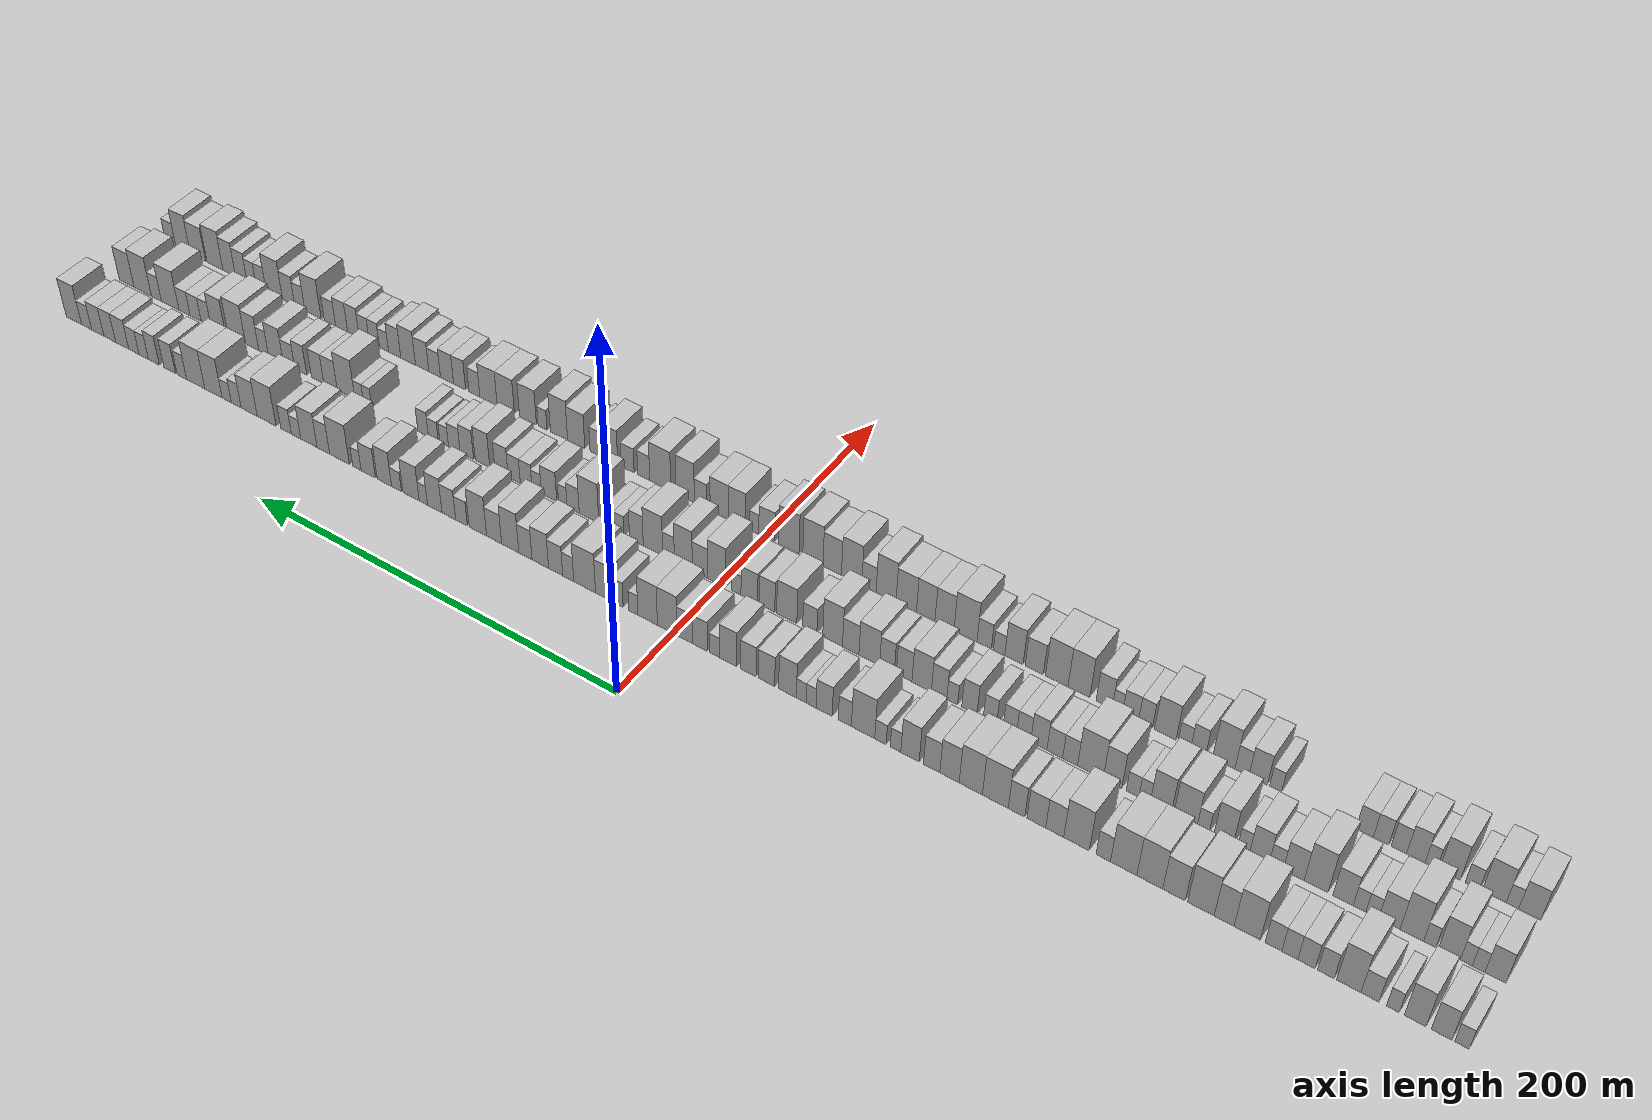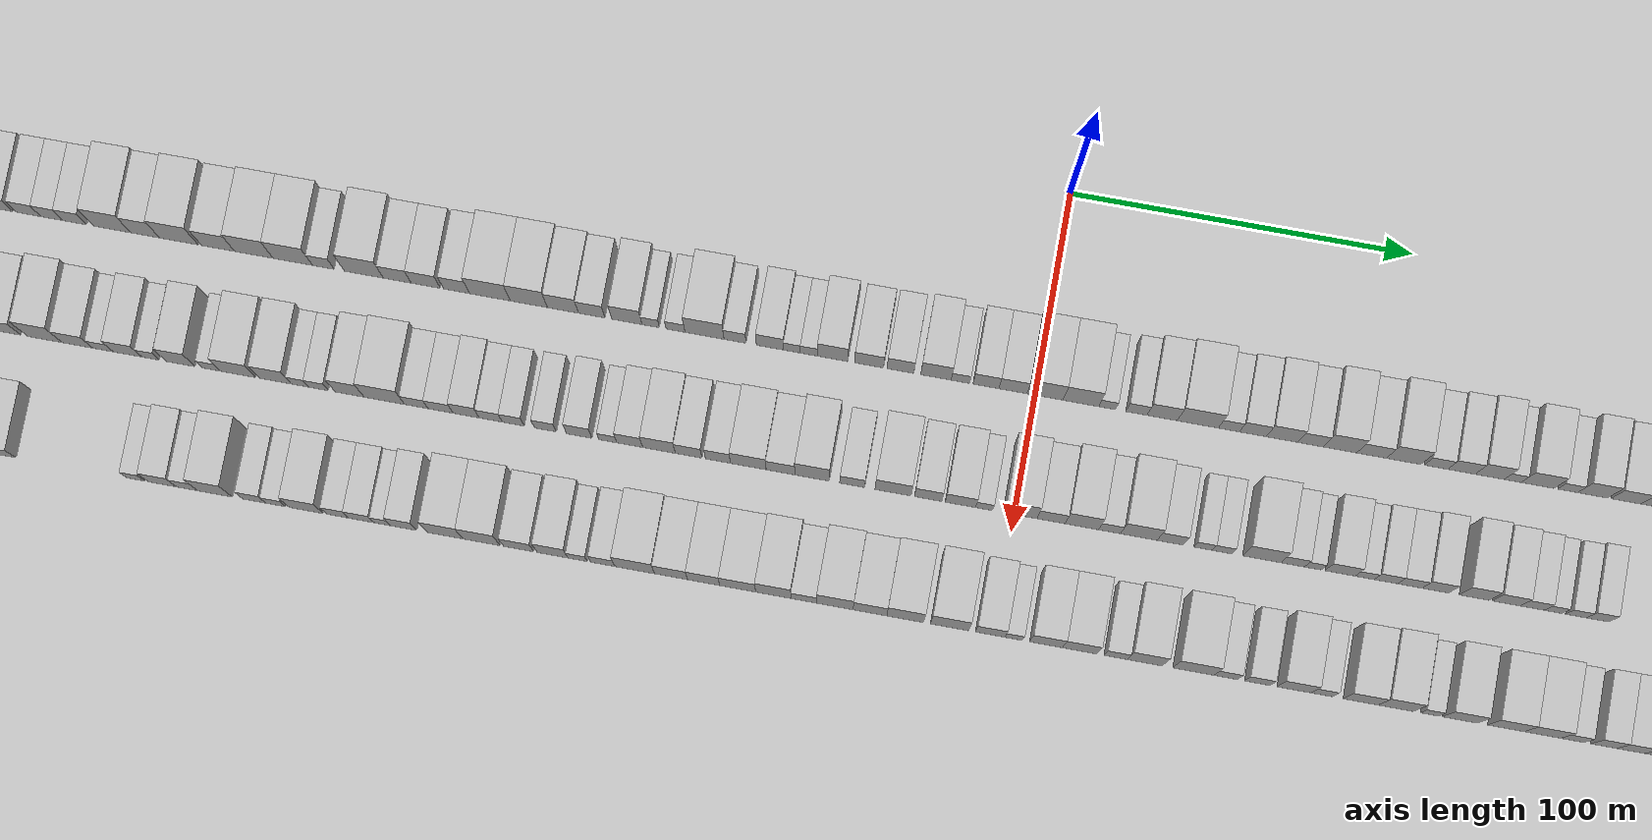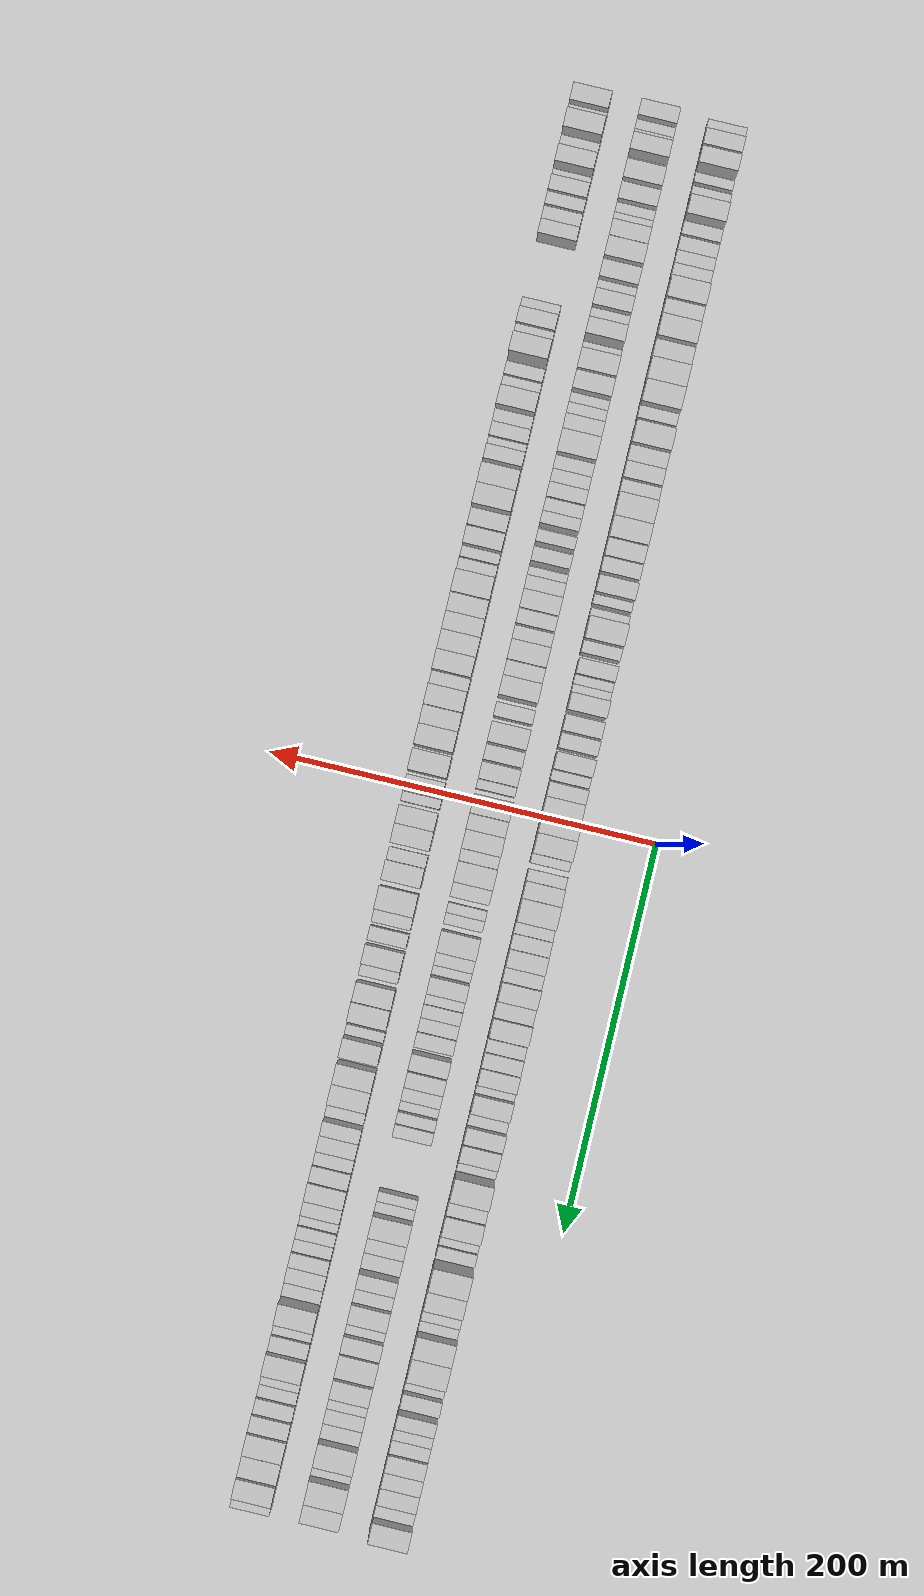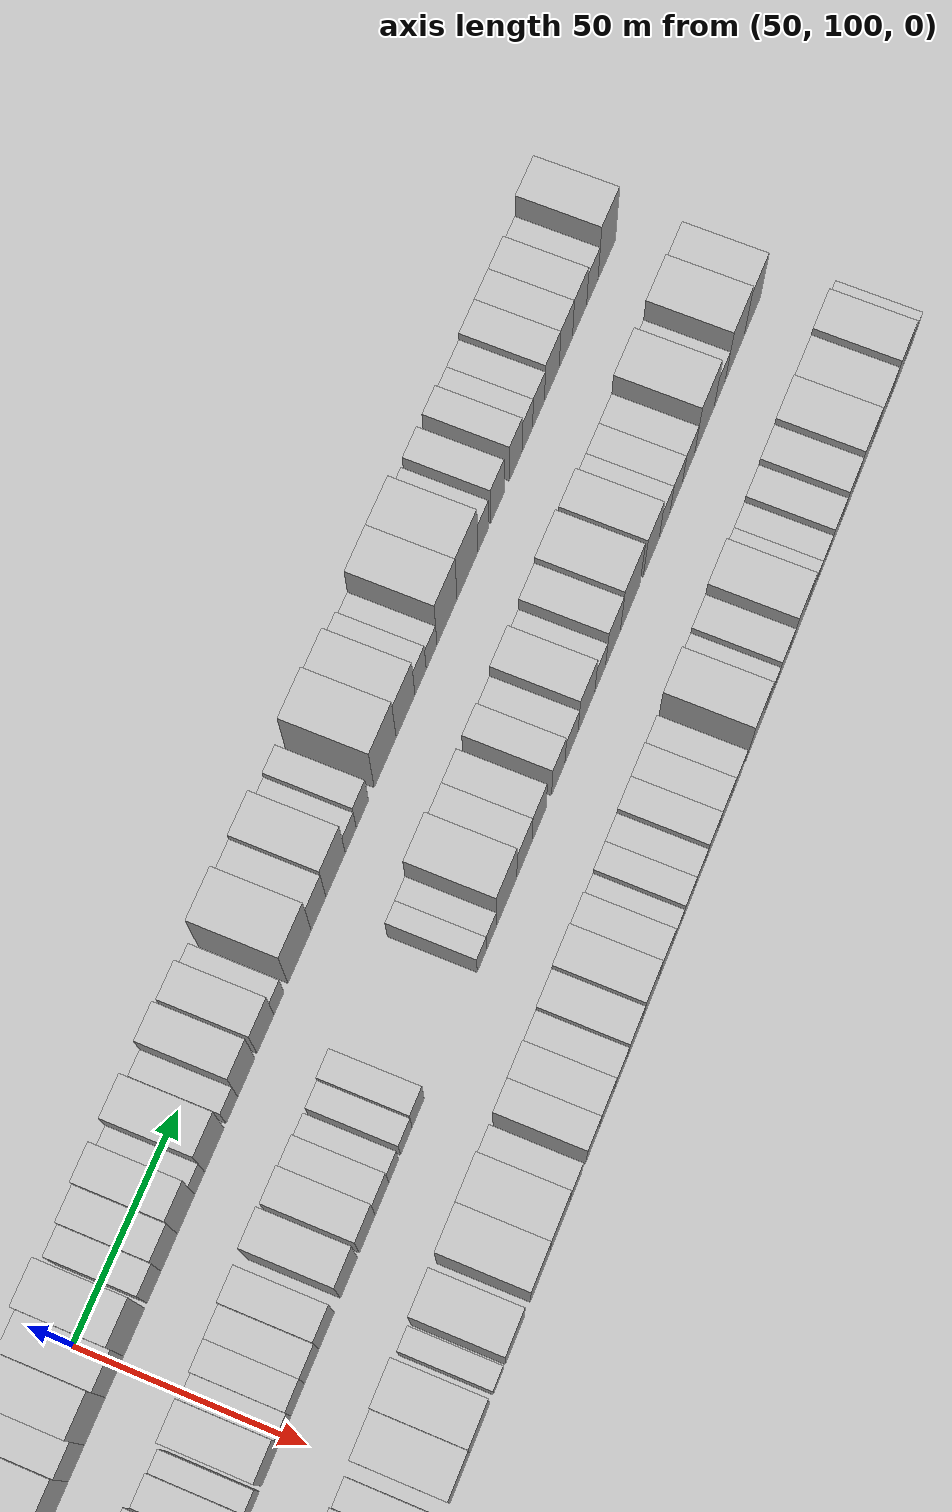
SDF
<sdf version="1.6">
 <world name="default">
  <scene>
   <sky><clouds><speed>12</speed></clouds></sky>
   <ambient>0.4 0.4 0.4 1</ambient>
   <background>0.7 0.7 0.7 1</background>
   <shadows>1</shadows>
  </scene>
  <gravity>0 0 -9.8066</gravity>
  <magnetic_field>6e-06 2.3e-05 -4.2e-05</magnetic_field>
  <physics default="0" name="default_physics" type="ode">
   <ode>
    <solver>
     <type>quick</type>
     <iters>10</iters>
     <sor>1.0</sor>
     <use_dynamic_moi_rescaling>0</use_dynamic_moi_rescaling>
    </solver>
    <constraints>
     <cfm>0</cfm>
     <erp>0.2</erp>
     <contact_max_correcting_vel>100</contact_max_correcting_vel>
     <contact_surface_layer>0.001</contact_surface_layer>
    </constraints>
   </ode>
   <max_step_size>0.004</max_step_size>
   <real_time_factor>1</real_time_factor>
   <real_time_update_rate>250</real_time_update_rate>
  </physics>
  <light name="sun" type="directional">
   <pose>0 0 10 0 0 0</pose>
   <diffuse>0.8 0.8 0.8 1</diffuse>
   <specular>0.2 0.2 0.2 1</specular>
   <attenuation>
    <range>1000</range>
    <constant>0.9</constant>
    <linear>0.01</linear>
    <quadratic>0.001</quadratic>
   </attenuation>
   <direction>-0.5 0.1 -0.9</direction>
  </light>
  <model name="building_1">
   <static>1</static>
   <pose>50.0000 -357.1473 0 0.000000 0.000000 0.000000</pose>
   <link name="link">
    <pose>0 0 6.00 0 0 0</pose>
    <collision name="collision"><geometry><box><size>20.0000 5.7055 12.0000</size></box></geometry></collision>
    <visual name="visual">
     <cast_shadows>0</cast_shadows>
     <geometry><box><size>20.0000 5.7055 12.0000</size></box></geometry>
     <material>
      <script>
       <uri>model://HANNAS_wall/materials/scripts</uri>
       <uri>model://HANNAS_wall/materials/textures</uri>
       <name>vrc/HANNAS_wall</name>
      </script>
     </material>
    </visual>
   </link>
  </model>
  <model name="building_2">
   <static>1</static>
   <pose>50.0000 -349.2135 0 0.000000 0.000000 0.000000</pose>
   <link name="link">
    <pose>0 0 9.00 0 0 0</pose>
    <collision name="collision"><geometry><box><size>20.0000 8.1621 18.0000</size></box></geometry></collision>
    <visual name="visual">
     <cast_shadows>0</cast_shadows>
     <geometry><box><size>20.0000 8.1621 18.0000</size></box></geometry>
     <material>
      <script>
       <uri>model://HANNAS_wall/materials/scripts</uri>
       <uri>model://HANNAS_wall/materials/textures</uri>
       <name>vrc/HANNAS_wall</name>
      </script>
     </material>
    </visual>
   </link>
  </model>
  <model name="building_3">
   <static>1</static>
   <pose>50.0000 -338.8269 0 0.000000 0.000000 0.000000</pose>
   <link name="link">
    <pose>0 0 10.50 0 0 0</pose>
    <collision name="collision"><geometry><box><size>20.0000 8.6111 21.0000</size></box></geometry></collision>
    <visual name="visual">
     <cast_shadows>0</cast_shadows>
     <geometry><box><size>20.0000 8.6111 21.0000</size></box></geometry>
     <material>
      <script>
       <uri>model://HANNAS_wall/materials/scripts</uri>
       <uri>model://HANNAS_wall/materials/textures</uri>
       <name>vrc/HANNAS_wall</name>
      </script>
     </material>
    </visual>
   </link>
  </model>
  <model name="building_4">
   <static>1</static>
   <pose>50.0000 -329.9672 0 0.000000 0.000000 0.000000</pose>
   <link name="link">
    <pose>0 0 6.00 0 0 0</pose>
    <collision name="collision"><geometry><box><size>20.0000 5.1084 12.0000</size></box></geometry></collision>
    <visual name="visual">
     <cast_shadows>0</cast_shadows>
     <geometry><box><size>20.0000 5.1084 12.0000</size></box></geometry>
     <material>
      <script>
       <uri>model://HANNAS_wall/materials/scripts</uri>
       <uri>model://HANNAS_wall/materials/textures</uri>
       <name>vrc/HANNAS_wall</name>
      </script>
     </material>
    </visual>
   </link>
  </model>
  <model name="building_5">
   <static>1</static>
   <pose>50.0000 -320.7984 0 0.000000 0.000000 0.000000</pose>
   <link name="link">
    <pose>0 0 7.50 0 0 0</pose>
    <collision name="collision"><geometry><box><size>20.0000 7.2293 15.0000</size></box></geometry></collision>
    <visual name="visual">
     <cast_shadows>0</cast_shadows>
     <geometry><box><size>20.0000 7.2293 15.0000</size></box></geometry>
     <material>
      <script>
       <uri>model://HANNAS_wall/materials/scripts</uri>
       <uri>model://HANNAS_wall/materials/textures</uri>
       <name>vrc/HANNAS_wall</name>
      </script>
     </material>
    </visual>
   </link>
  </model>
  <model name="building_6">
   <static>1</static>
   <pose>50.0000 -312.2470 0 0.000000 0.000000 0.000000</pose>
   <link name="link">
    <pose>0 0 12.00 0 0 0</pose>
    <collision name="collision"><geometry><box><size>20.0000 9.8735 24.0000</size></box></geometry></collision>
    <visual name="visual">
     <cast_shadows>0</cast_shadows>
     <geometry><box><size>20.0000 9.8735 24.0000</size></box></geometry>
     <material>
      <script>
       <uri>model://HANNAS_wall/materials/scripts</uri>
       <uri>model://HANNAS_wall/materials/textures</uri>
       <name>vrc/HANNAS_wall</name>
      </script>
     </material>
    </visual>
   </link>
  </model>
  <model name="building_7">
   <static>1</static>
   <pose>50.0000 -302.9227 0 0.000000 0.000000 0.000000</pose>
   <link name="link">
    <pose>0 0 7.50 0 0 0</pose>
    <collision name="collision"><geometry><box><size>20.0000 6.7750 15.0000</size></box></geometry></collision>
    <visual name="visual">
     <cast_shadows>0</cast_shadows>
     <geometry><box><size>20.0000 6.7750 15.0000</size></box></geometry>
     <material>
      <script>
       <uri>model://HANNAS_wall/materials/scripts</uri>
       <uri>model://HANNAS_wall/materials/textures</uri>
       <name>vrc/HANNAS_wall</name>
      </script>
     </material>
    </visual>
   </link>
  </model>
  <model name="building_8">
   <static>1</static>
   <pose>50.0000 -294.9445 0 0.000000 0.000000 0.000000</pose>
   <link name="link">
    <pose>0 0 7.50 0 0 0</pose>
    <collision name="collision"><geometry><box><size>20.0000 7.1815 15.0000</size></box></geometry></collision>
    <visual name="visual">
     <cast_shadows>0</cast_shadows>
     <geometry><box><size>20.0000 7.1815 15.0000</size></box></geometry>
     <material>
      <script>
       <uri>model://HANNAS_wall/materials/scripts</uri>
       <uri>model://HANNAS_wall/materials/textures</uri>
       <name>vrc/HANNAS_wall</name>
      </script>
     </material>
    </visual>
   </link>
  </model>
  <model name="building_9">
   <static>1</static>
   <pose>50.0000 -288.0629 0 0.000000 0.000000 0.000000</pose>
   <link name="link">
    <pose>0 0 7.50 0 0 0</pose>
    <collision name="collision"><geometry><box><size>20.0000 6.5817 15.0000</size></box></geometry></collision>
    <visual name="visual">
     <cast_shadows>0</cast_shadows>
     <geometry><box><size>20.0000 6.5817 15.0000</size></box></geometry>
     <material>
      <script>
       <uri>model://HANNAS_wall/materials/scripts</uri>
       <uri>model://HANNAS_wall/materials/textures</uri>
       <name>vrc/HANNAS_wall</name>
      </script>
     </material>
    </visual>
   </link>
  </model>
  <model name="building_10">
   <static>1</static>
   <pose>50.0000 -281.2849 0 0.000000 0.000000 0.000000</pose>
   <link name="link">
    <pose>0 0 7.50 0 0 0</pose>
    <collision name="collision"><geometry><box><size>20.0000 6.9745 15.0000</size></box></geometry></collision>
    <visual name="visual">
     <cast_shadows>0</cast_shadows>
     <geometry><box><size>20.0000 6.9745 15.0000</size></box></geometry>
     <material>
      <script>
       <uri>model://HANNAS_wall/materials/scripts</uri>
       <uri>model://HANNAS_wall/materials/textures</uri>
       <name>vrc/HANNAS_wall</name>
      </script>
     </material>
    </visual>
   </link>
  </model>
  <model name="building_11">
   <static>1</static>
   <pose>50.0000 -270.2725 0 0.000000 0.000000 0.000000</pose>
   <link name="link">
    <pose>0 0 12.00 0 0 0</pose>
    <collision name="collision"><geometry><box><size>20.0000 11.0504 24.0000</size></box></geometry></collision>
    <visual name="visual">
     <cast_shadows>0</cast_shadows>
     <geometry><box><size>20.0000 11.0504 24.0000</size></box></geometry>
     <material>
      <script>
       <uri>model://HANNAS_wall/materials/scripts</uri>
       <uri>model://HANNAS_wall/materials/textures</uri>
       <name>vrc/HANNAS_wall</name>
      </script>
     </material>
    </visual>
   </link>
  </model>
  <model name="building_12">
   <static>1</static>
   <pose>50.0000 -260.5234 0 0.000000 0.000000 0.000000</pose>
   <link name="link">
    <pose>0 0 10.50 0 0 0</pose>
    <collision name="collision"><geometry><box><size>20.0000 8.4478 21.0000</size></box></geometry></collision>
    <visual name="visual">
     <cast_shadows>0</cast_shadows>
     <geometry><box><size>20.0000 8.4478 21.0000</size></box></geometry>
     <material>
      <script>
       <uri>model://HANNAS_wall/materials/scripts</uri>
       <uri>model://HANNAS_wall/materials/textures</uri>
       <name>vrc/HANNAS_wall</name>
      </script>
     </material>
    </visual>
   </link>
  </model>
  <model name="building_13">
   <static>1</static>
   <pose>50.0000 -250.6275 0 0.000000 0.000000 0.000000</pose>
   <link name="link">
    <pose>0 0 12.00 0 0 0</pose>
    <collision name="collision"><geometry><box><size>20.0000 11.3440 24.0000</size></box></geometry></collision>
    <visual name="visual">
     <cast_shadows>0</cast_shadows>
     <geometry><box><size>20.0000 11.3440 24.0000</size></box></geometry>
     <material>
      <script>
       <uri>model://HANNAS_wall/materials/scripts</uri>
       <uri>model://HANNAS_wall/materials/textures</uri>
       <name>vrc/HANNAS_wall</name>
      </script>
     </material>
    </visual>
   </link>
  </model>
  <model name="building_14">
   <static>1</static>
   <pose>50.0000 -239.0872 0 0.000000 0.000000 0.000000</pose>
   <link name="link">
    <pose>0 0 10.50 0 0 0</pose>
    <collision name="collision"><geometry><box><size>20.0000 9.7365 21.0000</size></box></geometry></collision>
    <visual name="visual">
     <cast_shadows>0</cast_shadows>
     <geometry><box><size>20.0000 9.7365 21.0000</size></box></geometry>
     <material>
      <script>
       <uri>model://HANNAS_wall/materials/scripts</uri>
       <uri>model://HANNAS_wall/materials/textures</uri>
       <name>vrc/HANNAS_wall</name>
      </script>
     </material>
    </visual>
   </link>
  </model>
  <model name="building_15">
   <static>1</static>
   <pose>50.0000 -228.5402 0 0.000000 0.000000 0.000000</pose>
   <link name="link">
    <pose>0 0 12.00 0 0 0</pose>
    <collision name="collision"><geometry><box><size>20.0000 11.3576 24.0000</size></box></geometry></collision>
    <visual name="visual">
     <cast_shadows>0</cast_shadows>
     <geometry><box><size>20.0000 11.3576 24.0000</size></box></geometry>
     <material>
      <script>
       <uri>model://HANNAS_wall/materials/scripts</uri>
       <uri>model://HANNAS_wall/materials/textures</uri>
       <name>vrc/HANNAS_wall</name>
      </script>
     </material>
    </visual>
   </link>
  </model>
  <model name="building_16">
   <static>1</static>
   <pose>50.0000 -217.0679 0 0.000000 0.000000 0.000000</pose>
   <link name="link">
    <pose>0 0 12.00 0 0 0</pose>
    <collision name="collision"><geometry><box><size>20.0000 11.5871 24.0000</size></box></geometry></collision>
    <visual name="visual">
     <cast_shadows>0</cast_shadows>
     <geometry><box><size>20.0000 11.5871 24.0000</size></box></geometry>
     <material>
      <script>
       <uri>model://HANNAS_wall/materials/scripts</uri>
       <uri>model://HANNAS_wall/materials/textures</uri>
       <name>vrc/HANNAS_wall</name>
      </script>
     </material>
    </visual>
   </link>
  </model>
  <model name="building_17">
   <static>1</static>
   <pose>50.0000 -208.0867 0 0.000000 0.000000 0.000000</pose>
   <link name="link">
    <pose>0 0 7.50 0 0 0</pose>
    <collision name="collision"><geometry><box><size>20.0000 6.3753 15.0000</size></box></geometry></collision>
    <visual name="visual">
     <cast_shadows>0</cast_shadows>
     <geometry><box><size>20.0000 6.3753 15.0000</size></box></geometry>
     <material>
      <script>
       <uri>model://HANNAS_wall/materials/scripts</uri>
       <uri>model://HANNAS_wall/materials/textures</uri>
       <name>vrc/HANNAS_wall</name>
      </script>
     </material>
    </visual>
   </link>
  </model>
  <model name="building_18">
   <static>1</static>
   <pose>50.0000 -196.1646 0 0.000000 0.000000 0.000000</pose>
   <link name="link">
    <pose>0 0 12.00 0 0 0</pose>
    <collision name="collision"><geometry><box><size>20.0000 11.4688 24.0000</size></box></geometry></collision>
    <visual name="visual">
     <cast_shadows>0</cast_shadows>
     <geometry><box><size>20.0000 11.4688 24.0000</size></box></geometry>
     <material>
      <script>
       <uri>model://HANNAS_wall/materials/scripts</uri>
       <uri>model://HANNAS_wall/materials/textures</uri>
       <name>vrc/HANNAS_wall</name>
      </script>
     </material>
    </visual>
   </link>
  </model>
  <model name="building_19">
   <static>1</static>
   <pose>50.0000 -186.3429 0 0.000000 0.000000 0.000000</pose>
   <link name="link">
    <pose>0 0 9.00 0 0 0</pose>
    <collision name="collision"><geometry><box><size>20.0000 8.1747 18.0000</size></box></geometry></collision>
    <visual name="visual">
     <cast_shadows>0</cast_shadows>
     <geometry><box><size>20.0000 8.1747 18.0000</size></box></geometry>
     <material>
      <script>
       <uri>model://HANNAS_wall/materials/scripts</uri>
       <uri>model://HANNAS_wall/materials/textures</uri>
       <name>vrc/HANNAS_wall</name>
      </script>
     </material>
    </visual>
   </link>
  </model>
  <model name="building_20">
   <static>1</static>
   <pose>50.0000 -177.9876 0 0.000000 0.000000 0.000000</pose>
   <link name="link">
    <pose>0 0 9.00 0 0 0</pose>
    <collision name="collision"><geometry><box><size>20.0000 8.5359 18.0000</size></box></geometry></collision>
    <visual name="visual">
     <cast_shadows>0</cast_shadows>
     <geometry><box><size>20.0000 8.5359 18.0000</size></box></geometry>
     <material>
      <script>
       <uri>model://HANNAS_wall/materials/scripts</uri>
       <uri>model://HANNAS_wall/materials/textures</uri>
       <name>vrc/HANNAS_wall</name>
      </script>
     </material>
    </visual>
   </link>
  </model>
  <model name="building_21">
   <static>1</static>
   <pose>50.0000 -168.9230 0 0.000000 0.000000 0.000000</pose>
   <link name="link">
    <pose>0 0 9.00 0 0 0</pose>
    <collision name="collision"><geometry><box><size>20.0000 7.5933 18.0000</size></box></geometry></collision>
    <visual name="visual">
     <cast_shadows>0</cast_shadows>
     <geometry><box><size>20.0000 7.5933 18.0000</size></box></geometry>
     <material>
      <script>
       <uri>model://HANNAS_wall/materials/scripts</uri>
       <uri>model://HANNAS_wall/materials/textures</uri>
       <name>vrc/HANNAS_wall</name>
      </script>
     </material>
    </visual>
   </link>
  </model>
  <model name="building_22">
   <static>1</static>
   <pose>50.0000 -159.1426 0 0.000000 0.000000 0.000000</pose>
   <link name="link">
    <pose>0 0 12.00 0 0 0</pose>
    <collision name="collision"><geometry><box><size>20.0000 11.9675 24.0000</size></box></geometry></collision>
    <visual name="visual">
     <cast_shadows>0</cast_shadows>
     <geometry><box><size>20.0000 11.9675 24.0000</size></box></geometry>
     <material>
      <script>
       <uri>model://HANNAS_wall/materials/scripts</uri>
       <uri>model://HANNAS_wall/materials/textures</uri>
       <name>vrc/HANNAS_wall</name>
      </script>
     </material>
    </visual>
   </link>
  </model>
  <model name="building_23">
   <static>1</static>
   <pose>50.0000 -147.7311 0 0.000000 0.000000 0.000000</pose>
   <link name="link">
    <pose>0 0 12.00 0 0 0</pose>
    <collision name="collision"><geometry><box><size>20.0000 10.8554 24.0000</size></box></geometry></collision>
    <visual name="visual">
     <cast_shadows>0</cast_shadows>
     <geometry><box><size>20.0000 10.8554 24.0000</size></box></geometry>
     <material>
      <script>
       <uri>model://HANNAS_wall/materials/scripts</uri>
       <uri>model://HANNAS_wall/materials/textures</uri>
       <name>vrc/HANNAS_wall</name>
      </script>
     </material>
    </visual>
   </link>
  </model>
  <model name="building_24">
   <static>1</static>
   <pose>50.0000 -137.7497 0 0.000000 0.000000 0.000000</pose>
   <link name="link">
    <pose>0 0 10.50 0 0 0</pose>
    <collision name="collision"><geometry><box><size>20.0000 9.1074 21.0000</size></box></geometry></collision>
    <visual name="visual">
     <cast_shadows>0</cast_shadows>
     <geometry><box><size>20.0000 9.1074 21.0000</size></box></geometry>
     <material>
      <script>
       <uri>model://HANNAS_wall/materials/scripts</uri>
       <uri>model://HANNAS_wall/materials/textures</uri>
       <name>vrc/HANNAS_wall</name>
      </script>
     </material>
    </visual>
   </link>
  </model>
  <model name="building_25">
   <static>1</static>
   <pose>50.0000 -129.3136 0 0.000000 0.000000 0.000000</pose>
   <link name="link">
    <pose>0 0 9.00 0 0 0</pose>
    <collision name="collision"><geometry><box><size>20.0000 7.7648 18.0000</size></box></geometry></collision>
    <visual name="visual">
     <cast_shadows>0</cast_shadows>
     <geometry><box><size>20.0000 7.7648 18.0000</size></box></geometry>
     <material>
      <script>
       <uri>model://HANNAS_wall/materials/scripts</uri>
       <uri>model://HANNAS_wall/materials/textures</uri>
       <name>vrc/HANNAS_wall</name>
      </script>
     </material>
    </visual>
   </link>
  </model>
  <model name="building_26">
   <static>1</static>
   <pose>50.0000 -119.0147 0 0.000000 0.000000 0.000000</pose>
   <link name="link">
    <pose>0 0 10.50 0 0 0</pose>
    <collision name="collision"><geometry><box><size>20.0000 8.8330 21.0000</size></box></geometry></collision>
    <visual name="visual">
     <cast_shadows>0</cast_shadows>
     <geometry><box><size>20.0000 8.8330 21.0000</size></box></geometry>
     <material>
      <script>
       <uri>model://HANNAS_wall/materials/scripts</uri>
       <uri>model://HANNAS_wall/materials/textures</uri>
       <name>vrc/HANNAS_wall</name>
      </script>
     </material>
    </visual>
   </link>
  </model>
  <model name="building_27">
   <static>1</static>
   <pose>50.0000 -112.0766 0 0.000000 0.000000 0.000000</pose>
   <link name="link">
    <pose>0 0 6.00 0 0 0</pose>
    <collision name="collision"><geometry><box><size>20.0000 5.0432 12.0000</size></box></geometry></collision>
    <visual name="visual">
     <cast_shadows>0</cast_shadows>
     <geometry><box><size>20.0000 5.0432 12.0000</size></box></geometry>
     <material>
      <script>
       <uri>model://HANNAS_wall/materials/scripts</uri>
       <uri>model://HANNAS_wall/materials/textures</uri>
       <name>vrc/HANNAS_wall</name>
      </script>
     </material>
    </visual>
   </link>
  </model>
  <model name="building_28">
   <static>1</static>
   <pose>50.0000 -104.7980 0 0.000000 0.000000 0.000000</pose>
   <link name="link">
    <pose>0 0 6.00 0 0 0</pose>
    <collision name="collision"><geometry><box><size>20.0000 5.5138 12.0000</size></box></geometry></collision>
    <visual name="visual">
     <cast_shadows>0</cast_shadows>
     <geometry><box><size>20.0000 5.5138 12.0000</size></box></geometry>
     <material>
      <script>
       <uri>model://HANNAS_wall/materials/scripts</uri>
       <uri>model://HANNAS_wall/materials/textures</uri>
       <name>vrc/HANNAS_wall</name>
      </script>
     </material>
    </visual>
   </link>
  </model>
  <model name="building_29">
   <static>1</static>
   <pose>50.0000 -96.3448 0 0.000000 0.000000 0.000000</pose>
   <link name="link">
    <pose>0 0 12.00 0 0 0</pose>
    <collision name="collision"><geometry><box><size>20.0000 11.3927 24.0000</size></box></geometry></collision>
    <visual name="visual">
     <cast_shadows>0</cast_shadows>
     <geometry><box><size>20.0000 11.3927 24.0000</size></box></geometry>
     <material>
      <script>
       <uri>model://HANNAS_wall/materials/scripts</uri>
       <uri>model://HANNAS_wall/materials/textures</uri>
       <name>vrc/HANNAS_wall</name>
      </script>
     </material>
    </visual>
   </link>
  </model>
  <model name="building_30">
   <static>1</static>
   <pose>50.0000 -87.4244 0 0.000000 0.000000 0.000000</pose>
   <link name="link">
    <pose>0 0 7.50 0 0 0</pose>
    <collision name="collision"><geometry><box><size>20.0000 6.4481 15.0000</size></box></geometry></collision>
    <visual name="visual">
     <cast_shadows>0</cast_shadows>
     <geometry><box><size>20.0000 6.4481 15.0000</size></box></geometry>
     <material>
      <script>
       <uri>model://HANNAS_wall/materials/scripts</uri>
       <uri>model://HANNAS_wall/materials/textures</uri>
       <name>vrc/HANNAS_wall</name>
      </script>
     </material>
    </visual>
   </link>
  </model>
  <model name="building_31">
   <static>1</static>
   <pose>50.0000 -77.2165 0 0.000000 0.000000 0.000000</pose>
   <link name="link">
    <pose>0 0 9.00 0 0 0</pose>
    <collision name="collision"><geometry><box><size>20.0000 7.9678 18.0000</size></box></geometry></collision>
    <visual name="visual">
     <cast_shadows>0</cast_shadows>
     <geometry><box><size>20.0000 7.9678 18.0000</size></box></geometry>
     <material>
      <script>
       <uri>model://HANNAS_wall/materials/scripts</uri>
       <uri>model://HANNAS_wall/materials/textures</uri>
       <name>vrc/HANNAS_wall</name>
      </script>
     </material>
    </visual>
   </link>
  </model>
  <model name="building_32">
   <static>1</static>
   <pose>50.0000 -70.8102 0 0.000000 0.000000 0.000000</pose>
   <link name="link">
    <pose>0 0 6.00 0 0 0</pose>
    <collision name="collision"><geometry><box><size>20.0000 4.8449 12.0000</size></box></geometry></collision>
    <visual name="visual">
     <cast_shadows>0</cast_shadows>
     <geometry><box><size>20.0000 4.8449 12.0000</size></box></geometry>
     <material>
      <script>
       <uri>model://HANNAS_wall/materials/scripts</uri>
       <uri>model://HANNAS_wall/materials/textures</uri>
       <name>vrc/HANNAS_wall</name>
      </script>
     </material>
    </visual>
   </link>
  </model>
  <model name="building_33">
   <static>1</static>
   <pose>50.0000 -65.8977 0 0.000000 0.000000 0.000000</pose>
   <link name="link">
    <pose>0 0 6.00 0 0 0</pose>
    <collision name="collision"><geometry><box><size>20.0000 4.9800 12.0000</size></box></geometry></collision>
    <visual name="visual">
     <cast_shadows>0</cast_shadows>
     <geometry><box><size>20.0000 4.9800 12.0000</size></box></geometry>
     <material>
      <script>
       <uri>model://HANNAS_wall/materials/scripts</uri>
       <uri>model://HANNAS_wall/materials/textures</uri>
       <name>vrc/HANNAS_wall</name>
      </script>
     </material>
    </visual>
   </link>
  </model>
  <model name="building_34">
   <static>1</static>
   <pose>50.0000 -58.9646 0 0.000000 0.000000 0.000000</pose>
   <link name="link">
    <pose>0 0 10.50 0 0 0</pose>
    <collision name="collision"><geometry><box><size>20.0000 8.8863 21.0000</size></box></geometry></collision>
    <visual name="visual">
     <cast_shadows>0</cast_shadows>
     <geometry><box><size>20.0000 8.8863 21.0000</size></box></geometry>
     <material>
      <script>
       <uri>model://HANNAS_wall/materials/scripts</uri>
       <uri>model://HANNAS_wall/materials/textures</uri>
       <name>vrc/HANNAS_wall</name>
      </script>
     </material>
    </visual>
   </link>
  </model>
  <model name="building_35">
   <static>1</static>
   <pose>50.0000 -48.3044 0 0.000000 0.000000 0.000000</pose>
   <link name="link">
    <pose>0 0 9.00 0 0 0</pose>
    <collision name="collision"><geometry><box><size>20.0000 8.4340 18.0000</size></box></geometry></collision>
    <visual name="visual">
     <cast_shadows>0</cast_shadows>
     <geometry><box><size>20.0000 8.4340 18.0000</size></box></geometry>
     <material>
      <script>
       <uri>model://HANNAS_wall/materials/scripts</uri>
       <uri>model://HANNAS_wall/materials/textures</uri>
       <name>vrc/HANNAS_wall</name>
      </script>
     </material>
    </visual>
   </link>
  </model>
  <model name="building_36">
   <static>1</static>
   <pose>50.0000 -39.1806 0 0.000000 0.000000 0.000000</pose>
   <link name="link">
    <pose>0 0 9.00 0 0 0</pose>
    <collision name="collision"><geometry><box><size>20.0000 7.8136 18.0000</size></box></geometry></collision>
    <visual name="visual">
     <cast_shadows>0</cast_shadows>
     <geometry><box><size>20.0000 7.8136 18.0000</size></box></geometry>
     <material>
      <script>
       <uri>model://HANNAS_wall/materials/scripts</uri>
       <uri>model://HANNAS_wall/materials/textures</uri>
       <name>vrc/HANNAS_wall</name>
      </script>
     </material>
    </visual>
   </link>
  </model>
  <model name="building_37">
   <static>1</static>
   <pose>50.0000 -28.8370 0 0.000000 0.000000 0.000000</pose>
   <link name="link">
    <pose>0 0 10.50 0 0 0</pose>
    <collision name="collision"><geometry><box><size>20.0000 8.8737 21.0000</size></box></geometry></collision>
    <visual name="visual">
     <cast_shadows>0</cast_shadows>
     <geometry><box><size>20.0000 8.8737 21.0000</size></box></geometry>
     <material>
      <script>
       <uri>model://HANNAS_wall/materials/scripts</uri>
       <uri>model://HANNAS_wall/materials/textures</uri>
       <name>vrc/HANNAS_wall</name>
      </script>
     </material>
    </visual>
   </link>
  </model>
  <model name="building_38">
   <static>1</static>
   <pose>50.0000 -21.7184 0 0.000000 0.000000 0.000000</pose>
   <link name="link">
    <pose>0 0 6.00 0 0 0</pose>
    <collision name="collision"><geometry><box><size>20.0000 5.3636 12.0000</size></box></geometry></collision>
    <visual name="visual">
     <cast_shadows>0</cast_shadows>
     <geometry><box><size>20.0000 5.3636 12.0000</size></box></geometry>
     <material>
      <script>
       <uri>model://HANNAS_wall/materials/scripts</uri>
       <uri>model://HANNAS_wall/materials/textures</uri>
       <name>vrc/HANNAS_wall</name>
      </script>
     </material>
    </visual>
   </link>
  </model>
  <model name="building_39">
   <static>1</static>
   <pose>50.0000 -14.2941 0 0.000000 0.000000 0.000000</pose>
   <link name="link">
    <pose>0 0 9.00 0 0 0</pose>
    <collision name="collision"><geometry><box><size>20.0000 7.4851 18.0000</size></box></geometry></collision>
    <visual name="visual">
     <cast_shadows>0</cast_shadows>
     <geometry><box><size>20.0000 7.4851 18.0000</size></box></geometry>
     <material>
      <script>
       <uri>model://HANNAS_wall/materials/scripts</uri>
       <uri>model://HANNAS_wall/materials/textures</uri>
       <name>vrc/HANNAS_wall</name>
      </script>
     </material>
    </visual>
   </link>
  </model>
  <model name="building_40">
   <static>1</static>
   <pose>50.0000 -6.4519 0 0.000000 0.000000 0.000000</pose>
   <link name="link">
    <pose>0 0 9.00 0 0 0</pose>
    <collision name="collision"><geometry><box><size>20.0000 8.1993 18.0000</size></box></geometry></collision>
    <visual name="visual">
     <cast_shadows>0</cast_shadows>
     <geometry><box><size>20.0000 8.1993 18.0000</size></box></geometry>
     <material>
      <script>
       <uri>model://HANNAS_wall/materials/scripts</uri>
       <uri>model://HANNAS_wall/materials/textures</uri>
       <name>vrc/HANNAS_wall</name>
      </script>
     </material>
    </visual>
   </link>
  </model>
  <model name="building_41">
   <static>1</static>
   <pose>50.0000 2.8900 0 0.000000 0.000000 0.000000</pose>
   <link name="link">
    <pose>0 0 12.00 0 0 0</pose>
    <collision name="collision"><geometry><box><size>20.0000 10.4844 24.0000</size></box></geometry></collision>
    <visual name="visual">
     <cast_shadows>0</cast_shadows>
     <geometry><box><size>20.0000 10.4844 24.0000</size></box></geometry>
     <material>
      <script>
       <uri>model://HANNAS_wall/materials/scripts</uri>
       <uri>model://HANNAS_wall/materials/textures</uri>
       <name>vrc/HANNAS_wall</name>
      </script>
     </material>
    </visual>
   </link>
  </model>
  <model name="building_42">
   <static>1</static>
   <pose>50.0000 13.3271 0 0.000000 0.000000 0.000000</pose>
   <link name="link">
    <pose>0 0 12.00 0 0 0</pose>
    <collision name="collision"><geometry><box><size>20.0000 10.3897 24.0000</size></box></geometry></collision>
    <visual name="visual">
     <cast_shadows>0</cast_shadows>
     <geometry><box><size>20.0000 10.3897 24.0000</size></box></geometry>
     <material>
      <script>
       <uri>model://HANNAS_wall/materials/scripts</uri>
       <uri>model://HANNAS_wall/materials/textures</uri>
       <name>vrc/HANNAS_wall</name>
      </script>
     </material>
    </visual>
   </link>
  </model>
  <model name="building_43">
   <static>1</static>
   <pose>50.0000 20.9626 0 0.000000 0.000000 0.000000</pose>
   <link name="link">
    <pose>0 0 6.00 0 0 0</pose>
    <collision name="collision"><geometry><box><size>20.0000 4.8814 12.0000</size></box></geometry></collision>
    <visual name="visual">
     <cast_shadows>0</cast_shadows>
     <geometry><box><size>20.0000 4.8814 12.0000</size></box></geometry>
     <material>
      <script>
       <uri>model://HANNAS_wall/materials/scripts</uri>
       <uri>model://HANNAS_wall/materials/textures</uri>
       <name>vrc/HANNAS_wall</name>
      </script>
     </material>
    </visual>
   </link>
  </model>
  <model name="building_44">
   <static>1</static>
   <pose>50.0000 29.4781 0 0.000000 0.000000 0.000000</pose>
   <link name="link">
    <pose>0 0 7.50 0 0 0</pose>
    <collision name="collision"><geometry><box><size>20.0000 6.1497 15.0000</size></box></geometry></collision>
    <visual name="visual">
     <cast_shadows>0</cast_shadows>
     <geometry><box><size>20.0000 6.1497 15.0000</size></box></geometry>
     <material>
      <script>
       <uri>model://HANNAS_wall/materials/scripts</uri>
       <uri>model://HANNAS_wall/materials/textures</uri>
       <name>vrc/HANNAS_wall</name>
      </script>
     </material>
    </visual>
   </link>
  </model>
  <model name="building_45">
   <static>1</static>
   <pose>50.0000 36.9410 0 0.000000 0.000000 0.000000</pose>
   <link name="link">
    <pose>0 0 10.50 0 0 0</pose>
    <collision name="collision"><geometry><box><size>20.0000 8.7761 21.0000</size></box></geometry></collision>
    <visual name="visual">
     <cast_shadows>0</cast_shadows>
     <geometry><box><size>20.0000 8.7761 21.0000</size></box></geometry>
     <material>
      <script>
       <uri>model://HANNAS_wall/materials/scripts</uri>
       <uri>model://HANNAS_wall/materials/textures</uri>
       <name>vrc/HANNAS_wall</name>
      </script>
     </material>
    </visual>
   </link>
  </model>
  <model name="building_46">
   <static>1</static>
   <pose>50.0000 47.2723 0 0.000000 0.000000 0.000000</pose>
   <link name="link">
    <pose>0 0 12.00 0 0 0</pose>
    <collision name="collision"><geometry><box><size>20.0000 11.8866 24.0000</size></box></geometry></collision>
    <visual name="visual">
     <cast_shadows>0</cast_shadows>
     <geometry><box><size>20.0000 11.8866 24.0000</size></box></geometry>
     <material>
      <script>
       <uri>model://HANNAS_wall/materials/scripts</uri>
       <uri>model://HANNAS_wall/materials/textures</uri>
       <name>vrc/HANNAS_wall</name>
      </script>
     </material>
    </visual>
   </link>
  </model>
  <model name="building_47">
   <static>1</static>
   <pose>50.0000 56.2705 0 0.000000 0.000000 0.000000</pose>
   <link name="link">
    <pose>0 0 7.50 0 0 0</pose>
    <collision name="collision"><geometry><box><size>20.0000 6.1097 15.0000</size></box></geometry></collision>
    <visual name="visual">
     <cast_shadows>0</cast_shadows>
     <geometry><box><size>20.0000 6.1097 15.0000</size></box></geometry>
     <material>
      <script>
       <uri>model://HANNAS_wall/materials/scripts</uri>
       <uri>model://HANNAS_wall/materials/textures</uri>
       <name>vrc/HANNAS_wall</name>
      </script>
     </material>
    </visual>
   </link>
  </model>
  <model name="building_48">
   <static>1</static>
   <pose>50.0000 63.2182 0 0.000000 0.000000 0.000000</pose>
   <link name="link">
    <pose>0 0 9.00 0 0 0</pose>
    <collision name="collision"><geometry><box><size>20.0000 7.7858 18.0000</size></box></geometry></collision>
    <visual name="visual">
     <cast_shadows>0</cast_shadows>
     <geometry><box><size>20.0000 7.7858 18.0000</size></box></geometry>
     <material>
      <script>
       <uri>model://HANNAS_wall/materials/scripts</uri>
       <uri>model://HANNAS_wall/materials/textures</uri>
       <name>vrc/HANNAS_wall</name>
      </script>
     </material>
    </visual>
   </link>
  </model>
  <model name="building_49">
   <static>1</static>
   <pose>50.0000 71.7059 0 0.000000 0.000000 0.000000</pose>
   <link name="link">
    <pose>0 0 10.50 0 0 0</pose>
    <collision name="collision"><geometry><box><size>20.0000 9.1894 21.0000</size></box></geometry></collision>
    <visual name="visual">
     <cast_shadows>0</cast_shadows>
     <geometry><box><size>20.0000 9.1894 21.0000</size></box></geometry>
     <material>
      <script>
       <uri>model://HANNAS_wall/materials/scripts</uri>
       <uri>model://HANNAS_wall/materials/textures</uri>
       <name>vrc/HANNAS_wall</name>
      </script>
     </material>
    </visual>
   </link>
  </model>
  <model name="building_50">
   <static>1</static>
   <pose>50.0000 80.0003 0 0.000000 0.000000 0.000000</pose>
   <link name="link">
    <pose>0 0 9.00 0 0 0</pose>
    <collision name="collision"><geometry><box><size>20.0000 7.3994 18.0000</size></box></geometry></collision>
    <visual name="visual">
     <cast_shadows>0</cast_shadows>
     <geometry><box><size>20.0000 7.3994 18.0000</size></box></geometry>
     <material>
      <script>
       <uri>model://HANNAS_wall/materials/scripts</uri>
       <uri>model://HANNAS_wall/materials/textures</uri>
       <name>vrc/HANNAS_wall</name>
      </script>
     </material>
    </visual>
   </link>
  </model>
  <model name="building_51">
   <static>1</static>
   <pose>50.0000 88.5457 0 0.000000 0.000000 0.000000</pose>
   <link name="link">
    <pose>0 0 12.00 0 0 0</pose>
    <collision name="collision"><geometry><box><size>20.0000 9.6916 24.0000</size></box></geometry></collision>
    <visual name="visual">
     <cast_shadows>0</cast_shadows>
     <geometry><box><size>20.0000 9.6916 24.0000</size></box></geometry>
     <material>
      <script>
       <uri>model://HANNAS_wall/materials/scripts</uri>
       <uri>model://HANNAS_wall/materials/textures</uri>
       <name>vrc/HANNAS_wall</name>
      </script>
     </material>
    </visual>
   </link>
  </model>
  <model name="building_52">
   <static>1</static>
   <pose>50.0000 97.6655 0 0.000000 0.000000 0.000000</pose>
   <link name="link">
    <pose>0 0 9.00 0 0 0</pose>
    <collision name="collision"><geometry><box><size>20.0000 8.5480 18.0000</size></box></geometry></collision>
    <visual name="visual">
     <cast_shadows>0</cast_shadows>
     <geometry><box><size>20.0000 8.5480 18.0000</size></box></geometry>
     <material>
      <script>
       <uri>model://HANNAS_wall/materials/scripts</uri>
       <uri>model://HANNAS_wall/materials/textures</uri>
       <name>vrc/HANNAS_wall</name>
      </script>
     </material>
    </visual>
   </link>
  </model>
  <model name="building_53">
   <static>1</static>
   <pose>50.0000 106.9367 0 0.000000 0.000000 0.000000</pose>
   <link name="link">
    <pose>0 0 12.00 0 0 0</pose>
    <collision name="collision"><geometry><box><size>20.0000 9.9942 24.0000</size></box></geometry></collision>
    <visual name="visual">
     <cast_shadows>0</cast_shadows>
     <geometry><box><size>20.0000 9.9942 24.0000</size></box></geometry>
     <material>
      <script>
       <uri>model://HANNAS_wall/materials/scripts</uri>
       <uri>model://HANNAS_wall/materials/textures</uri>
       <name>vrc/HANNAS_wall</name>
      </script>
     </material>
    </visual>
   </link>
  </model>
  <model name="building_54">
   <static>1</static>
   <pose>50.0000 116.3106 0 0.000000 0.000000 0.000000</pose>
   <link name="link">
    <pose>0 0 7.50 0 0 0</pose>
    <collision name="collision"><geometry><box><size>20.0000 6.7537 15.0000</size></box></geometry></collision>
    <visual name="visual">
     <cast_shadows>0</cast_shadows>
     <geometry><box><size>20.0000 6.7537 15.0000</size></box></geometry>
     <material>
      <script>
       <uri>model://HANNAS_wall/materials/scripts</uri>
       <uri>model://HANNAS_wall/materials/textures</uri>
       <name>vrc/HANNAS_wall</name>
      </script>
     </material>
    </visual>
   </link>
  </model>
  <model name="building_55">
   <static>1</static>
   <pose>50.0000 123.6317 0 0.000000 0.000000 0.000000</pose>
   <link name="link">
    <pose>0 0 9.00 0 0 0</pose>
    <collision name="collision"><geometry><box><size>20.0000 7.8885 18.0000</size></box></geometry></collision>
    <visual name="visual">
     <cast_shadows>0</cast_shadows>
     <geometry><box><size>20.0000 7.8885 18.0000</size></box></geometry>
     <material>
      <script>
       <uri>model://HANNAS_wall/materials/scripts</uri>
       <uri>model://HANNAS_wall/materials/textures</uri>
       <name>vrc/HANNAS_wall</name>
      </script>
     </material>
    </visual>
   </link>
  </model>
  <model name="building_56">
   <static>1</static>
   <pose>50.0000 131.7996 0 0.000000 0.000000 0.000000</pose>
   <link name="link">
    <pose>0 0 10.50 0 0 0</pose>
    <collision name="collision"><geometry><box><size>20.0000 8.4473 21.0000</size></box></geometry></collision>
    <visual name="visual">
     <cast_shadows>0</cast_shadows>
     <geometry><box><size>20.0000 8.4473 21.0000</size></box></geometry>
     <material>
      <script>
       <uri>model://HANNAS_wall/materials/scripts</uri>
       <uri>model://HANNAS_wall/materials/textures</uri>
       <name>vrc/HANNAS_wall</name>
      </script>
     </material>
    </visual>
   </link>
  </model>
  <model name="building_57">
   <static>1</static>
   <pose>50.0000 138.4441 0 0.000000 0.000000 0.000000</pose>
   <link name="link">
    <pose>0 0 6.00 0 0 0</pose>
    <collision name="collision"><geometry><box><size>20.0000 4.8417 12.0000</size></box></geometry></collision>
    <visual name="visual">
     <cast_shadows>0</cast_shadows>
     <geometry><box><size>20.0000 4.8417 12.0000</size></box></geometry>
     <material>
      <script>
       <uri>model://HANNAS_wall/materials/scripts</uri>
       <uri>model://HANNAS_wall/materials/textures</uri>
       <name>vrc/HANNAS_wall</name>
      </script>
     </material>
    </visual>
   </link>
  </model>
  <model name="building_58">
   <static>1</static>
   <pose>50.0000 145.6218 0 0.000000 0.000000 0.000000</pose>
   <link name="link">
    <pose>0 0 10.50 0 0 0</pose>
    <collision name="collision"><geometry><box><size>20.0000 9.5137 21.0000</size></box></geometry></collision>
    <visual name="visual">
     <cast_shadows>0</cast_shadows>
     <geometry><box><size>20.0000 9.5137 21.0000</size></box></geometry>
     <material>
      <script>
       <uri>model://HANNAS_wall/materials/scripts</uri>
       <uri>model://HANNAS_wall/materials/textures</uri>
       <name>vrc/HANNAS_wall</name>
      </script>
     </material>
    </visual>
   </link>
  </model>
  <model name="building_59">
   <static>1</static>
   <pose>50.0000 154.2735 0 0.000000 0.000000 0.000000</pose>
   <link name="link">
    <pose>0 0 6.00 0 0 0</pose>
    <collision name="collision"><geometry><box><size>20.0000 5.7897 12.0000</size></box></geometry></collision>
    <visual name="visual">
     <cast_shadows>0</cast_shadows>
     <geometry><box><size>20.0000 5.7897 12.0000</size></box></geometry>
     <material>
      <script>
       <uri>model://HANNAS_wall/materials/scripts</uri>
       <uri>model://HANNAS_wall/materials/textures</uri>
       <name>vrc/HANNAS_wall</name>
      </script>
     </material>
    </visual>
   </link>
  </model>
  <model name="building_60">
   <static>1</static>
   <pose>50.0000 161.4640 0 0.000000 0.000000 0.000000</pose>
   <link name="link">
    <pose>0 0 10.50 0 0 0</pose>
    <collision name="collision"><geometry><box><size>20.0000 8.5913 21.0000</size></box></geometry></collision>
    <visual name="visual">
     <cast_shadows>0</cast_shadows>
     <geometry><box><size>20.0000 8.5913 21.0000</size></box></geometry>
     <material>
      <script>
       <uri>model://HANNAS_wall/materials/scripts</uri>
       <uri>model://HANNAS_wall/materials/textures</uri>
       <name>vrc/HANNAS_wall</name>
      </script>
     </material>
    </visual>
   </link>
  </model>
  <model name="building_61">
   <static>1</static>
   <pose>50.0000 171.0575 0 0.000000 0.000000 0.000000</pose>
   <link name="link">
    <pose>0 0 9.00 0 0 0</pose>
    <collision name="collision"><geometry><box><size>20.0000 8.5957 18.0000</size></box></geometry></collision>
    <visual name="visual">
     <cast_shadows>0</cast_shadows>
     <geometry><box><size>20.0000 8.5957 18.0000</size></box></geometry>
     <material>
      <script>
       <uri>model://HANNAS_wall/materials/scripts</uri>
       <uri>model://HANNAS_wall/materials/textures</uri>
       <name>vrc/HANNAS_wall</name>
      </script>
     </material>
    </visual>
   </link>
  </model>
  <model name="building_62">
   <static>1</static>
   <pose>50.0000 177.9104 0 0.000000 0.000000 0.000000</pose>
   <link name="link">
    <pose>0 0 6.00 0 0 0</pose>
    <collision name="collision"><geometry><box><size>20.0000 5.1101 12.0000</size></box></geometry></collision>
    <visual name="visual">
     <cast_shadows>0</cast_shadows>
     <geometry><box><size>20.0000 5.1101 12.0000</size></box></geometry>
     <material>
      <script>
       <uri>model://HANNAS_wall/materials/scripts</uri>
       <uri>model://HANNAS_wall/materials/textures</uri>
       <name>vrc/HANNAS_wall</name>
      </script>
     </material>
    </visual>
   </link>
  </model>
  <model name="building_63">
   <static>1</static>
   <pose>50.0000 188.4641 0 0.000000 0.000000 0.000000</pose>
   <link name="link">
    <pose>0 0 12.00 0 0 0</pose>
    <collision name="collision"><geometry><box><size>20.0000 11.9973 24.0000</size></box></geometry></collision>
    <visual name="visual">
     <cast_shadows>0</cast_shadows>
     <geometry><box><size>20.0000 11.9973 24.0000</size></box></geometry>
     <material>
      <script>
       <uri>model://HANNAS_wall/materials/scripts</uri>
       <uri>model://HANNAS_wall/materials/textures</uri>
       <name>vrc/HANNAS_wall</name>
      </script>
     </material>
    </visual>
   </link>
  </model>
  <model name="building_64">
   <static>1</static>
   <pose>50.0000 198.2894 0 0.000000 0.000000 0.000000</pose>
   <link name="link">
    <pose>0 0 9.00 0 0 0</pose>
    <collision name="collision"><geometry><box><size>20.0000 7.6532 18.0000</size></box></geometry></collision>
    <visual name="visual">
     <cast_shadows>0</cast_shadows>
     <geometry><box><size>20.0000 7.6532 18.0000</size></box></geometry>
     <material>
      <script>
       <uri>model://HANNAS_wall/materials/scripts</uri>
       <uri>model://HANNAS_wall/materials/textures</uri>
       <name>vrc/HANNAS_wall</name>
      </script>
     </material>
    </visual>
   </link>
  </model>
  <model name="building_65">
   <static>1</static>
   <pose>50.0000 207.1650 0 0.000000 0.000000 0.000000</pose>
   <link name="link">
    <pose>0 0 10.50 0 0 0</pose>
    <collision name="collision"><geometry><box><size>20.0000 10.0982 21.0000</size></box></geometry></collision>
    <visual name="visual">
     <cast_shadows>0</cast_shadows>
     <geometry><box><size>20.0000 10.0982 21.0000</size></box></geometry>
     <material>
      <script>
       <uri>model://HANNAS_wall/materials/scripts</uri>
       <uri>model://HANNAS_wall/materials/textures</uri>
       <name>vrc/HANNAS_wall</name>
      </script>
     </material>
    </visual>
   </link>
  </model>
  <model name="building_66">
   <static>1</static>
   <pose>50.0000 215.1283 0 0.000000 0.000000 0.000000</pose>
   <link name="link">
    <pose>0 0 6.00 0 0 0</pose>
    <collision name="collision"><geometry><box><size>20.0000 5.8283 12.0000</size></box></geometry></collision>
    <visual name="visual">
     <cast_shadows>0</cast_shadows>
     <geometry><box><size>20.0000 5.8283 12.0000</size></box></geometry>
     <material>
      <script>
       <uri>model://HANNAS_wall/materials/scripts</uri>
       <uri>model://HANNAS_wall/materials/textures</uri>
       <name>vrc/HANNAS_wall</name>
      </script>
     </material>
    </visual>
   </link>
  </model>
  <model name="building_67">
   <static>1</static>
   <pose>50.0000 221.2899 0 0.000000 0.000000 0.000000</pose>
   <link name="link">
    <pose>0 0 7.50 0 0 0</pose>
    <collision name="collision"><geometry><box><size>20.0000 6.4949 15.0000</size></box></geometry></collision>
    <visual name="visual">
     <cast_shadows>0</cast_shadows>
     <geometry><box><size>20.0000 6.4949 15.0000</size></box></geometry>
     <material>
      <script>
       <uri>model://HANNAS_wall/materials/scripts</uri>
       <uri>model://HANNAS_wall/materials/textures</uri>
       <name>vrc/HANNAS_wall</name>
      </script>
     </material>
    </visual>
   </link>
  </model>
  <model name="building_68">
   <static>1</static>
   <pose>50.0000 233.4532 0 0.000000 0.000000 0.000000</pose>
   <link name="link">
    <pose>0 0 12.00 0 0 0</pose>
    <collision name="collision"><geometry><box><size>20.0000 11.8316 24.0000</size></box></geometry></collision>
    <visual name="visual">
     <cast_shadows>0</cast_shadows>
     <geometry><box><size>20.0000 11.8316 24.0000</size></box></geometry>
     <material>
      <script>
       <uri>model://HANNAS_wall/materials/scripts</uri>
       <uri>model://HANNAS_wall/materials/textures</uri>
       <name>vrc/HANNAS_wall</name>
      </script>
     </material>
    </visual>
   </link>
  </model>
  <model name="building_69">
   <static>1</static>
   <pose>50.0000 244.4825 0 0.000000 0.000000 0.000000</pose>
   <link name="link">
    <pose>0 0 10.50 0 0 0</pose>
    <collision name="collision"><geometry><box><size>20.0000 10.2271 21.0000</size></box></geometry></collision>
    <visual name="visual">
     <cast_shadows>0</cast_shadows>
     <geometry><box><size>20.0000 10.2271 21.0000</size></box></geometry>
     <material>
      <script>
       <uri>model://HANNAS_wall/materials/scripts</uri>
       <uri>model://HANNAS_wall/materials/textures</uri>
       <name>vrc/HANNAS_wall</name>
      </script>
     </material>
    </visual>
   </link>
  </model>
  <model name="building_70">
   <static>1</static>
   <pose>50.0000 252.6746 0 0.000000 0.000000 0.000000</pose>
   <link name="link">
    <pose>0 0 7.50 0 0 0</pose>
    <collision name="collision"><geometry><box><size>20.0000 6.1571 15.0000</size></box></geometry></collision>
    <visual name="visual">
     <cast_shadows>0</cast_shadows>
     <geometry><box><size>20.0000 6.1571 15.0000</size></box></geometry>
     <material>
      <script>
       <uri>model://HANNAS_wall/materials/scripts</uri>
       <uri>model://HANNAS_wall/materials/textures</uri>
       <name>vrc/HANNAS_wall</name>
      </script>
     </material>
    </visual>
   </link>
  </model>
  <model name="building_71">
   <static>1</static>
   <pose>50.0000 258.7114 0 0.000000 0.000000 0.000000</pose>
   <link name="link">
    <pose>0 0 6.00 0 0 0</pose>
    <collision name="collision"><geometry><box><size>20.0000 5.9164 12.0000</size></box></geometry></collision>
    <visual name="visual">
     <cast_shadows>0</cast_shadows>
     <geometry><box><size>20.0000 5.9164 12.0000</size></box></geometry>
     <material>
      <script>
       <uri>model://HANNAS_wall/materials/scripts</uri>
       <uri>model://HANNAS_wall/materials/textures</uri>
       <name>vrc/HANNAS_wall</name>
      </script>
     </material>
    </visual>
   </link>
  </model>
  <model name="building_72">
   <static>1</static>
   <pose>50.0000 267.2373 0 0.000000 0.000000 0.000000</pose>
   <link name="link">
    <pose>0 0 12.00 0 0 0</pose>
    <collision name="collision"><geometry><box><size>20.0000 11.1354 24.0000</size></box></geometry></collision>
    <visual name="visual">
     <cast_shadows>0</cast_shadows>
     <geometry><box><size>20.0000 11.1354 24.0000</size></box></geometry>
     <material>
      <script>
       <uri>model://HANNAS_wall/materials/scripts</uri>
       <uri>model://HANNAS_wall/materials/textures</uri>
       <name>vrc/HANNAS_wall</name>
      </script>
     </material>
    </visual>
   </link>
  </model>
  <model name="building_73">
   <static>1</static>
   <pose>50.0000 278.6968 0 0.000000 0.000000 0.000000</pose>
   <link name="link">
    <pose>0 0 12.00 0 0 0</pose>
    <collision name="collision"><geometry><box><size>20.0000 11.7836 24.0000</size></box></geometry></collision>
    <visual name="visual">
     <cast_shadows>0</cast_shadows>
     <geometry><box><size>20.0000 11.7836 24.0000</size></box></geometry>
     <material>
      <script>
       <uri>model://HANNAS_wall/materials/scripts</uri>
       <uri>model://HANNAS_wall/materials/textures</uri>
       <name>vrc/HANNAS_wall</name>
      </script>
     </material>
    </visual>
   </link>
  </model>
  <model name="building_74">
   <static>1</static>
   <pose>50.0000 287.6970 0 0.000000 0.000000 0.000000</pose>
   <link name="link">
    <pose>0 0 7.50 0 0 0</pose>
    <collision name="collision"><geometry><box><size>20.0000 6.2170 15.0000</size></box></geometry></collision>
    <visual name="visual">
     <cast_shadows>0</cast_shadows>
     <geometry><box><size>20.0000 6.2170 15.0000</size></box></geometry>
     <material>
      <script>
       <uri>model://HANNAS_wall/materials/scripts</uri>
       <uri>model://HANNAS_wall/materials/textures</uri>
       <name>vrc/HANNAS_wall</name>
      </script>
     </material>
    </visual>
   </link>
  </model>
  <model name="building_75">
   <static>1</static>
   <pose>50.0000 295.6456 0 0.000000 0.000000 0.000000</pose>
   <link name="link">
    <pose>0 0 9.00 0 0 0</pose>
    <collision name="collision"><geometry><box><size>20.0000 7.6803 18.0000</size></box></geometry></collision>
    <visual name="visual">
     <cast_shadows>0</cast_shadows>
     <geometry><box><size>20.0000 7.6803 18.0000</size></box></geometry>
     <material>
      <script>
       <uri>model://HANNAS_wall/materials/scripts</uri>
       <uri>model://HANNAS_wall/materials/textures</uri>
       <name>vrc/HANNAS_wall</name>
      </script>
     </material>
    </visual>
   </link>
  </model>
  <model name="building_76">
   <static>1</static>
   <pose>50.0000 306.1095 0 0.000000 0.000000 0.000000</pose>
   <link name="link">
    <pose>0 0 9.00 0 0 0</pose>
    <collision name="collision"><geometry><box><size>20.0000 7.2474 18.0000</size></box></geometry></collision>
    <visual name="visual">
     <cast_shadows>0</cast_shadows>
     <geometry><box><size>20.0000 7.2474 18.0000</size></box></geometry>
     <material>
      <script>
       <uri>model://HANNAS_wall/materials/scripts</uri>
       <uri>model://HANNAS_wall/materials/textures</uri>
       <name>vrc/HANNAS_wall</name>
      </script>
     </material>
    </visual>
   </link>
  </model>
  <model name="building_77">
   <static>1</static>
   <pose>50.0000 312.8303 0 0.000000 0.000000 0.000000</pose>
   <link name="link">
    <pose>0 0 7.50 0 0 0</pose>
    <collision name="collision"><geometry><box><size>20.0000 6.1943 15.0000</size></box></geometry></collision>
    <visual name="visual">
     <cast_shadows>0</cast_shadows>
     <geometry><box><size>20.0000 6.1943 15.0000</size></box></geometry>
     <material>
      <script>
       <uri>model://HANNAS_wall/materials/scripts</uri>
       <uri>model://HANNAS_wall/materials/textures</uri>
       <name>vrc/HANNAS_wall</name>
      </script>
     </material>
    </visual>
   </link>
  </model>
  <model name="building_78">
   <static>1</static>
   <pose>50.0000 319.3700 0 0.000000 0.000000 0.000000</pose>
   <link name="link">
    <pose>0 0 7.50 0 0 0</pose>
    <collision name="collision"><geometry><box><size>20.0000 6.8851 15.0000</size></box></geometry></collision>
    <visual name="visual">
     <cast_shadows>0</cast_shadows>
     <geometry><box><size>20.0000 6.8851 15.0000</size></box></geometry>
     <material>
      <script>
       <uri>model://HANNAS_wall/materials/scripts</uri>
       <uri>model://HANNAS_wall/materials/textures</uri>
       <name>vrc/HANNAS_wall</name>
      </script>
     </material>
    </visual>
   </link>
  </model>
  <model name="building_79">
   <static>1</static>
   <pose>50.0000 327.1696 0 0.000000 0.000000 0.000000</pose>
   <link name="link">
    <pose>0 0 9.00 0 0 0</pose>
    <collision name="collision"><geometry><box><size>20.0000 8.7141 18.0000</size></box></geometry></collision>
    <visual name="visual">
     <cast_shadows>0</cast_shadows>
     <geometry><box><size>20.0000 8.7141 18.0000</size></box></geometry>
     <material>
      <script>
       <uri>model://HANNAS_wall/materials/scripts</uri>
       <uri>model://HANNAS_wall/materials/textures</uri>
       <name>vrc/HANNAS_wall</name>
      </script>
     </material>
    </visual>
   </link>
  </model>
  <model name="building_80">
   <static>1</static>
   <pose>50.0000 335.4508 0 0.000000 0.000000 0.000000</pose>
   <link name="link">
    <pose>0 0 9.00 0 0 0</pose>
    <collision name="collision"><geometry><box><size>20.0000 7.8483 18.0000</size></box></geometry></collision>
    <visual name="visual">
     <cast_shadows>0</cast_shadows>
     <geometry><box><size>20.0000 7.8483 18.0000</size></box></geometry>
     <material>
      <script>
       <uri>model://HANNAS_wall/materials/scripts</uri>
       <uri>model://HANNAS_wall/materials/textures</uri>
       <name>vrc/HANNAS_wall</name>
      </script>
     </material>
    </visual>
   </link>
  </model>
  <model name="building_81">
   <static>1</static>
   <pose>50.0000 343.5949 0 0.000000 0.000000 0.000000</pose>
   <link name="link">
    <pose>0 0 9.00 0 0 0</pose>
    <collision name="collision"><geometry><box><size>20.0000 8.4400 18.0000</size></box></geometry></collision>
    <visual name="visual">
     <cast_shadows>0</cast_shadows>
     <geometry><box><size>20.0000 8.4400 18.0000</size></box></geometry>
     <material>
      <script>
       <uri>model://HANNAS_wall/materials/scripts</uri>
       <uri>model://HANNAS_wall/materials/textures</uri>
       <name>vrc/HANNAS_wall</name>
      </script>
     </material>
    </visual>
   </link>
  </model>
  <model name="building_82">
   <static>1</static>
   <pose>50.0000 351.2537 0 0.000000 0.000000 0.000000</pose>
   <link name="link">
    <pose>0 0 7.50 0 0 0</pose>
    <collision name="collision"><geometry><box><size>20.0000 6.8775 15.0000</size></box></geometry></collision>
    <visual name="visual">
     <cast_shadows>0</cast_shadows>
     <geometry><box><size>20.0000 6.8775 15.0000</size></box></geometry>
     <material>
      <script>
       <uri>model://HANNAS_wall/materials/scripts</uri>
       <uri>model://HANNAS_wall/materials/textures</uri>
       <name>vrc/HANNAS_wall</name>
      </script>
     </material>
    </visual>
   </link>
  </model>
  <model name="building_83">
   <static>1</static>
   <pose>50.0000 359.9338 0 0.000000 0.000000 0.000000</pose>
   <link name="link">
    <pose>0 0 12.00 0 0 0</pose>
    <collision name="collision"><geometry><box><size>20.0000 10.4827 24.0000</size></box></geometry></collision>
    <visual name="visual">
     <cast_shadows>0</cast_shadows>
     <geometry><box><size>20.0000 10.4827 24.0000</size></box></geometry>
     <material>
      <script>
       <uri>model://HANNAS_wall/materials/scripts</uri>
       <uri>model://HANNAS_wall/materials/textures</uri>
       <name>vrc/HANNAS_wall</name>
      </script>
     </material>
    </visual>
   </link>
  </model>
  <model name="building_84">
   <static>1</static>
   <pose>85.0000 -355.8267 0 0.000000 0.000000 0.000000</pose>
   <link name="link">
    <pose>0 0 9.00 0 0 0</pose>
    <collision name="collision"><geometry><box><size>20.0000 8.3467 18.0000</size></box></geometry></collision>
    <visual name="visual">
     <cast_shadows>0</cast_shadows>
     <geometry><box><size>20.0000 8.3467 18.0000</size></box></geometry>
     <material>
      <script>
       <uri>model://HANNAS_wall/materials/scripts</uri>
       <uri>model://HANNAS_wall/materials/textures</uri>
       <name>vrc/HANNAS_wall</name>
      </script>
     </material>
    </visual>
   </link>
  </model>
  <model name="building_85">
   <static>1</static>
   <pose>85.0000 -349.1430 0 0.000000 0.000000 0.000000</pose>
   <link name="link">
    <pose>0 0 6.00 0 0 0</pose>
    <collision name="collision"><geometry><box><size>20.0000 5.0207 12.0000</size></box></geometry></collision>
    <visual name="visual">
     <cast_shadows>0</cast_shadows>
     <geometry><box><size>20.0000 5.0207 12.0000</size></box></geometry>
     <material>
      <script>
       <uri>model://HANNAS_wall/materials/scripts</uri>
       <uri>model://HANNAS_wall/materials/textures</uri>
       <name>vrc/HANNAS_wall</name>
      </script>
     </material>
    </visual>
   </link>
  </model>
  <model name="building_86">
   <static>1</static>
   <pose>85.0000 -344.2214 0 0.000000 0.000000 0.000000</pose>
   <link name="link">
    <pose>0 0 6.00 0 0 0</pose>
    <collision name="collision"><geometry><box><size>20.0000 4.8224 12.0000</size></box></geometry></collision>
    <visual name="visual">
     <cast_shadows>0</cast_shadows>
     <geometry><box><size>20.0000 4.8224 12.0000</size></box></geometry>
     <material>
      <script>
       <uri>model://HANNAS_wall/materials/scripts</uri>
       <uri>model://HANNAS_wall/materials/textures</uri>
       <name>vrc/HANNAS_wall</name>
      </script>
     </material>
    </visual>
   </link>
  </model>
  <model name="building_87">
   <static>1</static>
   <pose>85.0000 -337.4208 0 0.000000 0.000000 0.000000</pose>
   <link name="link">
    <pose>0 0 10.50 0 0 0</pose>
    <collision name="collision"><geometry><box><size>20.0000 8.7788 21.0000</size></box></geometry></collision>
    <visual name="visual">
     <cast_shadows>0</cast_shadows>
     <geometry><box><size>20.0000 8.7788 21.0000</size></box></geometry>
     <material>
      <script>
       <uri>model://HANNAS_wall/materials/scripts</uri>
       <uri>model://HANNAS_wall/materials/textures</uri>
       <name>vrc/HANNAS_wall</name>
      </script>
     </material>
    </visual>
   </link>
  </model>
  <model name="building_88">
   <static>1</static>
   <pose>85.0000 -329.5567 0 0.000000 0.000000 0.000000</pose>
   <link name="link">
    <pose>0 0 6.00 0 0 0</pose>
    <collision name="collision"><geometry><box><size>20.0000 4.9494 12.0000</size></box></geometry></collision>
    <visual name="visual">
     <cast_shadows>0</cast_shadows>
     <geometry><box><size>20.0000 4.9494 12.0000</size></box></geometry>
     <material>
      <script>
       <uri>model://HANNAS_wall/materials/scripts</uri>
       <uri>model://HANNAS_wall/materials/textures</uri>
       <name>vrc/HANNAS_wall</name>
      </script>
     </material>
    </visual>
   </link>
  </model>
  <model name="building_89">
   <static>1</static>
   <pose>85.0000 -322.2527 0 0.000000 0.000000 0.000000</pose>
   <link name="link">
    <pose>0 0 12.00 0 0 0</pose>
    <collision name="collision"><geometry><box><size>20.0000 9.6586 24.0000</size></box></geometry></collision>
    <visual name="visual">
     <cast_shadows>0</cast_shadows>
     <geometry><box><size>20.0000 9.6586 24.0000</size></box></geometry>
     <material>
      <script>
       <uri>model://HANNAS_wall/materials/scripts</uri>
       <uri>model://HANNAS_wall/materials/textures</uri>
       <name>vrc/HANNAS_wall</name>
      </script>
     </material>
    </visual>
   </link>
  </model>
  <model name="building_90">
   <static>1</static>
   <pose>85.0000 -313.0131 0 0.000000 0.000000 0.000000</pose>
   <link name="link">
    <pose>0 0 9.00 0 0 0</pose>
    <collision name="collision"><geometry><box><size>20.0000 8.8206 18.0000</size></box></geometry></collision>
    <visual name="visual">
     <cast_shadows>0</cast_shadows>
     <geometry><box><size>20.0000 8.8206 18.0000</size></box></geometry>
     <material>
      <script>
       <uri>model://HANNAS_wall/materials/scripts</uri>
       <uri>model://HANNAS_wall/materials/textures</uri>
       <name>vrc/HANNAS_wall</name>
      </script>
     </material>
    </visual>
   </link>
  </model>
  <model name="building_91">
   <static>1</static>
   <pose>85.0000 -305.9966 0 0.000000 0.000000 0.000000</pose>
   <link name="link">
    <pose>0 0 6.00 0 0 0</pose>
    <collision name="collision"><geometry><box><size>20.0000 5.2122 12.0000</size></box></geometry></collision>
    <visual name="visual">
     <cast_shadows>0</cast_shadows>
     <geometry><box><size>20.0000 5.2122 12.0000</size></box></geometry>
     <material>
      <script>
       <uri>model://HANNAS_wall/materials/scripts</uri>
       <uri>model://HANNAS_wall/materials/textures</uri>
       <name>vrc/HANNAS_wall</name>
      </script>
     </material>
    </visual>
   </link>
  </model>
  <model name="building_92">
   <static>1</static>
   <pose>85.0000 -300.7433 0 0.000000 0.000000 0.000000</pose>
   <link name="link">
    <pose>0 0 6.00 0 0 0</pose>
    <collision name="collision"><geometry><box><size>20.0000 5.2944 12.0000</size></box></geometry></collision>
    <visual name="visual">
     <cast_shadows>0</cast_shadows>
     <geometry><box><size>20.0000 5.2944 12.0000</size></box></geometry>
     <material>
      <script>
       <uri>model://HANNAS_wall/materials/scripts</uri>
       <uri>model://HANNAS_wall/materials/textures</uri>
       <name>vrc/HANNAS_wall</name>
      </script>
     </material>
    </visual>
   </link>
  </model>
  <model name="building_93">
   <static>1</static>
   <pose>85.0000 -293.8392 0 0.000000 0.000000 0.000000</pose>
   <link name="link">
    <pose>0 0 9.00 0 0 0</pose>
    <collision name="collision"><geometry><box><size>20.0000 8.5138 18.0000</size></box></geometry></collision>
    <visual name="visual">
     <cast_shadows>0</cast_shadows>
     <geometry><box><size>20.0000 8.5138 18.0000</size></box></geometry>
     <material>
      <script>
       <uri>model://HANNAS_wall/materials/scripts</uri>
       <uri>model://HANNAS_wall/materials/textures</uri>
       <name>vrc/HANNAS_wall</name>
      </script>
     </material>
    </visual>
   </link>
  </model>
  <model name="building_94">
   <static>1</static>
   <pose>85.0000 -282.5141 0 0.000000 0.000000 0.000000</pose>
   <link name="link">
    <pose>0 0 12.00 0 0 0</pose>
    <collision name="collision"><geometry><box><size>20.0000 10.1366 24.0000</size></box></geometry></collision>
    <visual name="visual">
     <cast_shadows>0</cast_shadows>
     <geometry><box><size>20.0000 10.1366 24.0000</size></box></geometry>
     <material>
      <script>
       <uri>model://HANNAS_wall/materials/scripts</uri>
       <uri>model://HANNAS_wall/materials/textures</uri>
       <name>vrc/HANNAS_wall</name>
      </script>
     </material>
    </visual>
   </link>
  </model>
  <model name="building_95">
   <static>1</static>
   <pose>85.0000 -272.9851 0 0.000000 0.000000 0.000000</pose>
   <link name="link">
    <pose>0 0 9.00 0 0 0</pose>
    <collision name="collision"><geometry><box><size>20.0000 8.9213 18.0000</size></box></geometry></collision>
    <visual name="visual">
     <cast_shadows>0</cast_shadows>
     <geometry><box><size>20.0000 8.9213 18.0000</size></box></geometry>
     <material>
      <script>
       <uri>model://HANNAS_wall/materials/scripts</uri>
       <uri>model://HANNAS_wall/materials/textures</uri>
       <name>vrc/HANNAS_wall</name>
      </script>
     </material>
    </visual>
   </link>
  </model>
  <model name="building_96">
   <static>1</static>
   <pose>85.0000 -265.5346 0 0.000000 0.000000 0.000000</pose>
   <link name="link">
    <pose>0 0 6.00 0 0 0</pose>
    <collision name="collision"><geometry><box><size>20.0000 5.9797 12.0000</size></box></geometry></collision>
    <visual name="visual">
     <cast_shadows>0</cast_shadows>
     <geometry><box><size>20.0000 5.9797 12.0000</size></box></geometry>
     <material>
      <script>
       <uri>model://HANNAS_wall/materials/scripts</uri>
       <uri>model://HANNAS_wall/materials/textures</uri>
       <name>vrc/HANNAS_wall</name>
      </script>
     </material>
    </visual>
   </link>
  </model>
  <model name="building_97">
   <static>1</static>
   <pose>85.0000 -258.3247 0 0.000000 0.000000 0.000000</pose>
   <link name="link">
    <pose>0 0 9.00 0 0 0</pose>
    <collision name="collision"><geometry><box><size>20.0000 8.4402 18.0000</size></box></geometry></collision>
    <visual name="visual">
     <cast_shadows>0</cast_shadows>
     <geometry><box><size>20.0000 8.4402 18.0000</size></box></geometry>
     <material>
      <script>
       <uri>model://HANNAS_wall/materials/scripts</uri>
       <uri>model://HANNAS_wall/materials/textures</uri>
       <name>vrc/HANNAS_wall</name>
      </script>
     </material>
    </visual>
   </link>
  </model>
  <model name="building_98">
   <static>1</static>
   <pose>85.0000 -251.5241 0 0.000000 0.000000 0.000000</pose>
   <link name="link">
    <pose>0 0 6.00 0 0 0</pose>
    <collision name="collision"><geometry><box><size>20.0000 5.1610 12.0000</size></box></geometry></collision>
    <visual name="visual">
     <cast_shadows>0</cast_shadows>
     <geometry><box><size>20.0000 5.1610 12.0000</size></box></geometry>
     <material>
      <script>
       <uri>model://HANNAS_wall/materials/scripts</uri>
       <uri>model://HANNAS_wall/materials/textures</uri>
       <name>vrc/HANNAS_wall</name>
      </script>
     </material>
    </visual>
   </link>
  </model>
  <model name="building_99">
   <static>1</static>
   <pose>85.0000 -242.7093 0 0.000000 0.000000 0.000000</pose>
   <link name="link">
    <pose>0 0 10.50 0 0 0</pose>
    <collision name="collision"><geometry><box><size>20.0000 8.4685 21.0000</size></box></geometry></collision>
    <visual name="visual">
     <cast_shadows>0</cast_shadows>
     <geometry><box><size>20.0000 8.4685 21.0000</size></box></geometry>
     <material>
      <script>
       <uri>model://HANNAS_wall/materials/scripts</uri>
       <uri>model://HANNAS_wall/materials/textures</uri>
       <name>vrc/HANNAS_wall</name>
      </script>
     </material>
    </visual>
   </link>
  </model>
  <model name="building_100">
   <static>1</static>
   <pose>85.0000 -233.8208 0 0.000000 0.000000 0.000000</pose>
   <link name="link">
    <pose>0 0 6.00 0 0 0</pose>
    <collision name="collision"><geometry><box><size>20.0000 5.3086 12.0000</size></box></geometry></collision>
    <visual name="visual">
     <cast_shadows>0</cast_shadows>
     <geometry><box><size>20.0000 5.3086 12.0000</size></box></geometry>
     <material>
      <script>
       <uri>model://HANNAS_wall/materials/scripts</uri>
       <uri>model://HANNAS_wall/materials/textures</uri>
       <name>vrc/HANNAS_wall</name>
      </script>
     </material>
    </visual>
   </link>
  </model>
  <model name="building_101">
   <static>1</static>
   <pose>85.0000 -225.9499 0 0.000000 0.000000 0.000000</pose>
   <link name="link">
    <pose>0 0 10.50 0 0 0</pose>
    <collision name="collision"><geometry><box><size>20.0000 10.4331 21.0000</size></box></geometry></collision>
    <visual name="visual">
     <cast_shadows>0</cast_shadows>
     <geometry><box><size>20.0000 10.4331 21.0000</size></box></geometry>
     <material>
      <script>
       <uri>model://HANNAS_wall/materials/scripts</uri>
       <uri>model://HANNAS_wall/materials/textures</uri>
       <name>vrc/HANNAS_wall</name>
      </script>
     </material>
    </visual>
   </link>
  </model>
  <model name="building_102">
   <static>1</static>
   <pose>85.0000 -215.0166 0 0.000000 0.000000 0.000000</pose>
   <link name="link">
    <pose>0 0 10.50 0 0 0</pose>
    <collision name="collision"><geometry><box><size>20.0000 9.4335 21.0000</size></box></geometry></collision>
    <visual name="visual">
     <cast_shadows>0</cast_shadows>
     <geometry><box><size>20.0000 9.4335 21.0000</size></box></geometry>
     <material>
      <script>
       <uri>model://HANNAS_wall/materials/scripts</uri>
       <uri>model://HANNAS_wall/materials/textures</uri>
       <name>vrc/HANNAS_wall</name>
      </script>
     </material>
    </visual>
   </link>
  </model>
  <model name="building_103">
   <static>1</static>
   <pose>85.0000 -207.7648 0 0.000000 0.000000 0.000000</pose>
   <link name="link">
    <pose>0 0 6.00 0 0 0</pose>
    <collision name="collision"><geometry><box><size>20.0000 5.0701 12.0000</size></box></geometry></collision>
    <visual name="visual">
     <cast_shadows>0</cast_shadows>
     <geometry><box><size>20.0000 5.0701 12.0000</size></box></geometry>
     <material>
      <script>
       <uri>model://HANNAS_wall/materials/scripts</uri>
       <uri>model://HANNAS_wall/materials/textures</uri>
       <name>vrc/HANNAS_wall</name>
      </script>
     </material>
    </visual>
   </link>
  </model>
  <model name="building_104">
   <static>1</static>
   <pose>85.0000 -202.3518 0 0.000000 0.000000 0.000000</pose>
   <link name="link">
    <pose>0 0 6.00 0 0 0</pose>
    <collision name="collision"><geometry><box><size>20.0000 5.7560 12.0000</size></box></geometry></collision>
    <visual name="visual">
     <cast_shadows>0</cast_shadows>
     <geometry><box><size>20.0000 5.7560 12.0000</size></box></geometry>
     <material>
      <script>
       <uri>model://HANNAS_wall/materials/scripts</uri>
       <uri>model://HANNAS_wall/materials/textures</uri>
       <name>vrc/HANNAS_wall</name>
      </script>
     </material>
    </visual>
   </link>
  </model>
  <model name="building_105">
   <static>1</static>
   <pose>85.0000 -193.2441 0 0.000000 0.000000 0.000000</pose>
   <link name="link">
    <pose>0 0 10.50 0 0 0</pose>
    <collision name="collision"><geometry><box><size>20.0000 8.4593 21.0000</size></box></geometry></collision>
    <visual name="visual">
     <cast_shadows>0</cast_shadows>
     <geometry><box><size>20.0000 8.4593 21.0000</size></box></geometry>
     <material>
      <script>
       <uri>model://HANNAS_wall/materials/scripts</uri>
       <uri>model://HANNAS_wall/materials/textures</uri>
       <name>vrc/HANNAS_wall</name>
      </script>
     </material>
    </visual>
   </link>
  </model>
  <model name="building_106">
   <static>1</static>
   <pose>85.0000 -183.0956 0 0.000000 0.000000 0.000000</pose>
   <link name="link">
    <pose>0 0 12.00 0 0 0</pose>
    <collision name="collision"><geometry><box><size>20.0000 11.8378 24.0000</size></box></geometry></collision>
    <visual name="visual">
     <cast_shadows>0</cast_shadows>
     <geometry><box><size>20.0000 11.8378 24.0000</size></box></geometry>
     <material>
      <script>
       <uri>model://HANNAS_wall/materials/scripts</uri>
       <uri>model://HANNAS_wall/materials/textures</uri>
       <name>vrc/HANNAS_wall</name>
      </script>
     </material>
    </visual>
   </link>
  </model>
  <model name="building_107">
   <static>1</static>
   <pose>85.0000 -173.7411 0 0.000000 0.000000 0.000000</pose>
   <link name="link">
    <pose>0 0 7.50 0 0 0</pose>
    <collision name="collision"><geometry><box><size>20.0000 6.8710 15.0000</size></box></geometry></collision>
    <visual name="visual">
     <cast_shadows>0</cast_shadows>
     <geometry><box><size>20.0000 6.8710 15.0000</size></box></geometry>
     <material>
      <script>
       <uri>model://HANNAS_wall/materials/scripts</uri>
       <uri>model://HANNAS_wall/materials/textures</uri>
       <name>vrc/HANNAS_wall</name>
      </script>
     </material>
    </visual>
   </link>
  </model>
  <model name="building_108">
   <static>1</static>
   <pose>85.0000 -166.6475 0 0.000000 0.000000 0.000000</pose>
   <link name="link">
    <pose>0 0 7.50 0 0 0</pose>
    <collision name="collision"><geometry><box><size>20.0000 7.3164 15.0000</size></box></geometry></collision>
    <visual name="visual">
     <cast_shadows>0</cast_shadows>
     <geometry><box><size>20.0000 7.3164 15.0000</size></box></geometry>
     <material>
      <script>
       <uri>model://HANNAS_wall/materials/scripts</uri>
       <uri>model://HANNAS_wall/materials/textures</uri>
       <name>vrc/HANNAS_wall</name>
      </script>
     </material>
    </visual>
   </link>
  </model>
  <model name="building_109">
   <static>1</static>
   <pose>85.0000 -159.1864 0 0.000000 0.000000 0.000000</pose>
   <link name="link">
    <pose>0 0 9.00 0 0 0</pose>
    <collision name="collision"><geometry><box><size>20.0000 7.6057 18.0000</size></box></geometry></collision>
    <visual name="visual">
     <cast_shadows>0</cast_shadows>
     <geometry><box><size>20.0000 7.6057 18.0000</size></box></geometry>
     <material>
      <script>
       <uri>model://HANNAS_wall/materials/scripts</uri>
       <uri>model://HANNAS_wall/materials/textures</uri>
       <name>vrc/HANNAS_wall</name>
      </script>
     </material>
    </visual>
   </link>
  </model>
  <model name="building_110">
   <static>1</static>
   <pose>85.0000 -152.0241 0 0.000000 0.000000 0.000000</pose>
   <link name="link">
    <pose>0 0 7.50 0 0 0</pose>
    <collision name="collision"><geometry><box><size>20.0000 6.7189 15.0000</size></box></geometry></collision>
    <visual name="visual">
     <cast_shadows>0</cast_shadows>
     <geometry><box><size>20.0000 6.7189 15.0000</size></box></geometry>
     <material>
      <script>
       <uri>model://HANNAS_wall/materials/scripts</uri>
       <uri>model://HANNAS_wall/materials/textures</uri>
       <name>vrc/HANNAS_wall</name>
      </script>
     </material>
    </visual>
   </link>
  </model>
  <model name="building_111">
   <static>1</static>
   <pose>85.0000 -145.4629 0 0.000000 0.000000 0.000000</pose>
   <link name="link">
    <pose>0 0 7.50 0 0 0</pose>
    <collision name="collision"><geometry><box><size>20.0000 6.4036 15.0000</size></box></geometry></collision>
    <visual name="visual">
     <cast_shadows>0</cast_shadows>
     <geometry><box><size>20.0000 6.4036 15.0000</size></box></geometry>
     <material>
      <script>
       <uri>model://HANNAS_wall/materials/scripts</uri>
       <uri>model://HANNAS_wall/materials/textures</uri>
       <name>vrc/HANNAS_wall</name>
      </script>
     </material>
    </visual>
   </link>
  </model>
  <model name="building_112">
   <static>1</static>
   <pose>85.0000 -136.0691 0 0.000000 0.000000 0.000000</pose>
   <link name="link">
    <pose>0 0 7.50 0 0 0</pose>
    <collision name="collision"><geometry><box><size>20.0000 6.3841 15.0000</size></box></geometry></collision>
    <visual name="visual">
     <cast_shadows>0</cast_shadows>
     <geometry><box><size>20.0000 6.3841 15.0000</size></box></geometry>
     <material>
      <script>
       <uri>model://HANNAS_wall/materials/scripts</uri>
       <uri>model://HANNAS_wall/materials/textures</uri>
       <name>vrc/HANNAS_wall</name>
      </script>
     </material>
    </visual>
   </link>
  </model>
  <model name="building_113">
   <static>1</static>
   <pose>85.0000 -126.2025 0 0.000000 0.000000 0.000000</pose>
   <link name="link">
    <pose>0 0 9.00 0 0 0</pose>
    <collision name="collision"><geometry><box><size>20.0000 7.3492 18.0000</size></box></geometry></collision>
    <visual name="visual">
     <cast_shadows>0</cast_shadows>
     <geometry><box><size>20.0000 7.3492 18.0000</size></box></geometry>
     <material>
      <script>
       <uri>model://HANNAS_wall/materials/scripts</uri>
       <uri>model://HANNAS_wall/materials/textures</uri>
       <name>vrc/HANNAS_wall</name>
      </script>
     </material>
    </visual>
   </link>
  </model>
  <model name="building_114">
   <static>1</static>
   <pose>85.0000 -117.9055 0 0.000000 0.000000 0.000000</pose>
   <link name="link">
    <pose>0 0 6.00 0 0 0</pose>
    <collision name="collision"><geometry><box><size>20.0000 5.2447 12.0000</size></box></geometry></collision>
    <visual name="visual">
     <cast_shadows>0</cast_shadows>
     <geometry><box><size>20.0000 5.2447 12.0000</size></box></geometry>
     <material>
      <script>
       <uri>model://HANNAS_wall/materials/scripts</uri>
       <uri>model://HANNAS_wall/materials/textures</uri>
       <name>vrc/HANNAS_wall</name>
      </script>
     </material>
    </visual>
   </link>
  </model>
  <model name="building_115">
   <static>1</static>
   <pose>85.0000 -111.5228 0 0.000000 0.000000 0.000000</pose>
   <link name="link">
    <pose>0 0 9.00 0 0 0</pose>
    <collision name="collision"><geometry><box><size>20.0000 7.5206 18.0000</size></box></geometry></collision>
    <visual name="visual">
     <cast_shadows>0</cast_shadows>
     <geometry><box><size>20.0000 7.5206 18.0000</size></box></geometry>
     <material>
      <script>
       <uri>model://HANNAS_wall/materials/scripts</uri>
       <uri>model://HANNAS_wall/materials/textures</uri>
       <name>vrc/HANNAS_wall</name>
      </script>
     </material>
    </visual>
   </link>
  </model>
  <model name="building_116">
   <static>1</static>
   <pose>85.0000 -103.0057 0 0.000000 0.000000 0.000000</pose>
   <link name="link">
    <pose>0 0 10.50 0 0 0</pose>
    <collision name="collision"><geometry><box><size>20.0000 9.5137 21.0000</size></box></geometry></collision>
    <visual name="visual">
     <cast_shadows>0</cast_shadows>
     <geometry><box><size>20.0000 9.5137 21.0000</size></box></geometry>
     <material>
      <script>
       <uri>model://HANNAS_wall/materials/scripts</uri>
       <uri>model://HANNAS_wall/materials/textures</uri>
       <name>vrc/HANNAS_wall</name>
      </script>
     </material>
    </visual>
   </link>
  </model>
  <model name="building_117">
   <static>1</static>
   <pose>85.0000 -94.3867 0 0.000000 0.000000 0.000000</pose>
   <link name="link">
    <pose>0 0 9.00 0 0 0</pose>
    <collision name="collision"><geometry><box><size>20.0000 7.7243 18.0000</size></box></geometry></collision>
    <visual name="visual">
     <cast_shadows>0</cast_shadows>
     <geometry><box><size>20.0000 7.7243 18.0000</size></box></geometry>
     <material>
      <script>
       <uri>model://HANNAS_wall/materials/scripts</uri>
       <uri>model://HANNAS_wall/materials/textures</uri>
       <name>vrc/HANNAS_wall</name>
      </script>
     </material>
    </visual>
   </link>
  </model>
  <model name="building_118">
   <static>1</static>
   <pose>85.0000 -85.8840 0 0.000000 0.000000 0.000000</pose>
   <link name="link">
    <pose>0 0 9.00 0 0 0</pose>
    <collision name="collision"><geometry><box><size>20.0000 7.2810 18.0000</size></box></geometry></collision>
    <visual name="visual">
     <cast_shadows>0</cast_shadows>
     <geometry><box><size>20.0000 7.2810 18.0000</size></box></geometry>
     <material>
      <script>
       <uri>model://HANNAS_wall/materials/scripts</uri>
       <uri>model://HANNAS_wall/materials/textures</uri>
       <name>vrc/HANNAS_wall</name>
      </script>
     </material>
    </visual>
   </link>
  </model>
  <model name="building_119">
   <static>1</static>
   <pose>85.0000 -77.0616 0 0.000000 0.000000 0.000000</pose>
   <link name="link">
    <pose>0 0 10.50 0 0 0</pose>
    <collision name="collision"><geometry><box><size>20.0000 10.3640 21.0000</size></box></geometry></collision>
    <visual name="visual">
     <cast_shadows>0</cast_shadows>
     <geometry><box><size>20.0000 10.3640 21.0000</size></box></geometry>
     <material>
      <script>
       <uri>model://HANNAS_wall/materials/scripts</uri>
       <uri>model://HANNAS_wall/materials/textures</uri>
       <name>vrc/HANNAS_wall</name>
      </script>
     </material>
    </visual>
   </link>
  </model>
  <model name="building_120">
   <static>1</static>
   <pose>85.0000 -67.7225 0 0.000000 0.000000 0.000000</pose>
   <link name="link">
    <pose>0 0 9.00 0 0 0</pose>
    <collision name="collision"><geometry><box><size>20.0000 8.3142 18.0000</size></box></geometry></collision>
    <visual name="visual">
     <cast_shadows>0</cast_shadows>
     <geometry><box><size>20.0000 8.3142 18.0000</size></box></geometry>
     <material>
      <script>
       <uri>model://HANNAS_wall/materials/scripts</uri>
       <uri>model://HANNAS_wall/materials/textures</uri>
       <name>vrc/HANNAS_wall</name>
      </script>
     </material>
    </visual>
   </link>
  </model>
  <model name="building_121">
   <static>1</static>
   <pose>85.0000 -58.5630 0 0.000000 0.000000 0.000000</pose>
   <link name="link">
    <pose>0 0 12.00 0 0 0</pose>
    <collision name="collision"><geometry><box><size>20.0000 10.0049 24.0000</size></box></geometry></collision>
    <visual name="visual">
     <cast_shadows>0</cast_shadows>
     <geometry><box><size>20.0000 10.0049 24.0000</size></box></geometry>
     <material>
      <script>
       <uri>model://HANNAS_wall/materials/scripts</uri>
       <uri>model://HANNAS_wall/materials/textures</uri>
       <name>vrc/HANNAS_wall</name>
      </script>
     </material>
    </visual>
   </link>
  </model>
  <model name="building_122">
   <static>1</static>
   <pose>85.0000 -46.9334 0 0.000000 0.000000 0.000000</pose>
   <link name="link">
    <pose>0 0 7.50 0 0 0</pose>
    <collision name="collision"><geometry><box><size>20.0000 7.2543 15.0000</size></box></geometry></collision>
    <visual name="visual">
     <cast_shadows>0</cast_shadows>
     <geometry><box><size>20.0000 7.2543 15.0000</size></box></geometry>
     <material>
      <script>
       <uri>model://HANNAS_wall/materials/scripts</uri>
       <uri>model://HANNAS_wall/materials/textures</uri>
       <name>vrc/HANNAS_wall</name>
      </script>
     </material>
    </visual>
   </link>
  </model>
  <model name="building_123">
   <static>1</static>
   <pose>85.0000 -35.0860 0 0.000000 0.000000 0.000000</pose>
   <link name="link">
    <pose>0 0 10.50 0 0 0</pose>
    <collision name="collision"><geometry><box><size>20.0000 10.4404 21.0000</size></box></geometry></collision>
    <visual name="visual">
     <cast_shadows>0</cast_shadows>
     <geometry><box><size>20.0000 10.4404 21.0000</size></box></geometry>
     <material>
      <script>
       <uri>model://HANNAS_wall/materials/scripts</uri>
       <uri>model://HANNAS_wall/materials/textures</uri>
       <name>vrc/HANNAS_wall</name>
      </script>
     </material>
    </visual>
   </link>
  </model>
  <model name="building_124">
   <static>1</static>
   <pose>85.0000 -24.9152 0 0.000000 0.000000 0.000000</pose>
   <link name="link">
    <pose>0 0 9.00 0 0 0</pose>
    <collision name="collision"><geometry><box><size>20.0000 7.9013 18.0000</size></box></geometry></collision>
    <visual name="visual">
     <cast_shadows>0</cast_shadows>
     <geometry><box><size>20.0000 7.9013 18.0000</size></box></geometry>
     <material>
      <script>
       <uri>model://HANNAS_wall/materials/scripts</uri>
       <uri>model://HANNAS_wall/materials/textures</uri>
       <name>vrc/HANNAS_wall</name>
      </script>
     </material>
    </visual>
   </link>
  </model>
  <model name="building_125">
   <static>1</static>
   <pose>85.0000 -15.5747 0 0.000000 0.000000 0.000000</pose>
   <link name="link">
    <pose>0 0 9.00 0 0 0</pose>
    <collision name="collision"><geometry><box><size>20.0000 8.7797 18.0000</size></box></geometry></collision>
    <visual name="visual">
     <cast_shadows>0</cast_shadows>
     <geometry><box><size>20.0000 8.7797 18.0000</size></box></geometry>
     <material>
      <script>
       <uri>model://HANNAS_wall/materials/scripts</uri>
       <uri>model://HANNAS_wall/materials/textures</uri>
       <name>vrc/HANNAS_wall</name>
      </script>
     </material>
    </visual>
   </link>
  </model>
  <model name="building_126">
   <static>1</static>
   <pose>85.0000 -8.7260 0 0.000000 0.000000 0.000000</pose>
   <link name="link">
    <pose>0 0 6.00 0 0 0</pose>
    <collision name="collision"><geometry><box><size>20.0000 4.9177 12.0000</size></box></geometry></collision>
    <visual name="visual">
     <cast_shadows>0</cast_shadows>
     <geometry><box><size>20.0000 4.9177 12.0000</size></box></geometry>
     <material>
      <script>
       <uri>model://HANNAS_wall/materials/scripts</uri>
       <uri>model://HANNAS_wall/materials/textures</uri>
       <name>vrc/HANNAS_wall</name>
      </script>
     </material>
    </visual>
   </link>
  </model>
  <model name="building_127">
   <static>1</static>
   <pose>85.0000 1.6451 0 0.000000 0.000000 0.000000</pose>
   <link name="link">
    <pose>0 0 12.00 0 0 0</pose>
    <collision name="collision"><geometry><box><size>20.0000 9.8245 24.0000</size></box></geometry></collision>
    <visual name="visual">
     <cast_shadows>0</cast_shadows>
     <geometry><box><size>20.0000 9.8245 24.0000</size></box></geometry>
     <material>
      <script>
       <uri>model://HANNAS_wall/materials/scripts</uri>
       <uri>model://HANNAS_wall/materials/textures</uri>
       <name>vrc/HANNAS_wall</name>
      </script>
     </material>
    </visual>
   </link>
  </model>
  <model name="building_128">
   <static>1</static>
   <pose>85.0000 10.6261 0 0.000000 0.000000 0.000000</pose>
   <link name="link">
    <pose>0 0 9.00 0 0 0</pose>
    <collision name="collision"><geometry><box><size>20.0000 8.1376 18.0000</size></box></geometry></collision>
    <visual name="visual">
     <cast_shadows>0</cast_shadows>
     <geometry><box><size>20.0000 8.1376 18.0000</size></box></geometry>
     <material>
      <script>
       <uri>model://HANNAS_wall/materials/scripts</uri>
       <uri>model://HANNAS_wall/materials/textures</uri>
       <name>vrc/HANNAS_wall</name>
      </script>
     </material>
    </visual>
   </link>
  </model>
  <model name="building_129">
   <static>1</static>
   <pose>85.0000 19.5484 0 0.000000 0.000000 0.000000</pose>
   <link name="link">
    <pose>0 0 12.00 0 0 0</pose>
    <collision name="collision"><geometry><box><size>20.0000 9.7070 24.0000</size></box></geometry></collision>
    <visual name="visual">
     <cast_shadows>0</cast_shadows>
     <geometry><box><size>20.0000 9.7070 24.0000</size></box></geometry>
     <material>
      <script>
       <uri>model://HANNAS_wall/materials/scripts</uri>
       <uri>model://HANNAS_wall/materials/textures</uri>
       <name>vrc/HANNAS_wall</name>
      </script>
     </material>
    </visual>
   </link>
  </model>
  <model name="building_130">
   <static>1</static>
   <pose>85.0000 27.5702 0 0.000000 0.000000 0.000000</pose>
   <link name="link">
    <pose>0 0 7.50 0 0 0</pose>
    <collision name="collision"><geometry><box><size>20.0000 6.3366 15.0000</size></box></geometry></collision>
    <visual name="visual">
     <cast_shadows>0</cast_shadows>
     <geometry><box><size>20.0000 6.3366 15.0000</size></box></geometry>
     <material>
      <script>
       <uri>model://HANNAS_wall/materials/scripts</uri>
       <uri>model://HANNAS_wall/materials/textures</uri>
       <name>vrc/HANNAS_wall</name>
      </script>
     </material>
    </visual>
   </link>
  </model>
  <model name="building_131">
   <static>1</static>
   <pose>85.0000 36.0484 0 0.000000 0.000000 0.000000</pose>
   <link name="link">
    <pose>0 0 12.00 0 0 0</pose>
    <collision name="collision"><geometry><box><size>20.0000 10.6198 24.0000</size></box></geometry></collision>
    <visual name="visual">
     <cast_shadows>0</cast_shadows>
     <geometry><box><size>20.0000 10.6198 24.0000</size></box></geometry>
     <material>
      <script>
       <uri>model://HANNAS_wall/materials/scripts</uri>
       <uri>model://HANNAS_wall/materials/textures</uri>
       <name>vrc/HANNAS_wall</name>
      </script>
     </material>
    </visual>
   </link>
  </model>
  <model name="building_132">
   <static>1</static>
   <pose>85.0000 45.1411 0 0.000000 0.000000 0.000000</pose>
   <link name="link">
    <pose>0 0 9.00 0 0 0</pose>
    <collision name="collision"><geometry><box><size>20.0000 7.5656 18.0000</size></box></geometry></collision>
    <visual name="visual">
     <cast_shadows>0</cast_shadows>
     <geometry><box><size>20.0000 7.5656 18.0000</size></box></geometry>
     <material>
      <script>
       <uri>model://HANNAS_wall/materials/scripts</uri>
       <uri>model://HANNAS_wall/materials/textures</uri>
       <name>vrc/HANNAS_wall</name>
      </script>
     </material>
    </visual>
   </link>
  </model>
  <model name="building_133">
   <static>1</static>
   <pose>85.0000 54.5978 0 0.000000 0.000000 0.000000</pose>
   <link name="link">
    <pose>0 0 6.00 0 0 0</pose>
    <collision name="collision"><geometry><box><size>20.0000 5.3477 12.0000</size></box></geometry></collision>
    <visual name="visual">
     <cast_shadows>0</cast_shadows>
     <geometry><box><size>20.0000 5.3477 12.0000</size></box></geometry>
     <material>
      <script>
       <uri>model://HANNAS_wall/materials/scripts</uri>
       <uri>model://HANNAS_wall/materials/textures</uri>
       <name>vrc/HANNAS_wall</name>
      </script>
     </material>
    </visual>
   </link>
  </model>
  <model name="building_134">
   <static>1</static>
   <pose>85.0000 60.1131 0 0.000000 0.000000 0.000000</pose>
   <link name="link">
    <pose>0 0 6.00 0 0 0</pose>
    <collision name="collision"><geometry><box><size>20.0000 5.6829 12.0000</size></box></geometry></collision>
    <visual name="visual">
     <cast_shadows>0</cast_shadows>
     <geometry><box><size>20.0000 5.6829 12.0000</size></box></geometry>
     <material>
      <script>
       <uri>model://HANNAS_wall/materials/scripts</uri>
       <uri>model://HANNAS_wall/materials/textures</uri>
       <name>vrc/HANNAS_wall</name>
      </script>
     </material>
    </visual>
   </link>
  </model>
  <model name="building_135">
   <static>1</static>
   <pose>85.0000 71.4660 0 0.000000 0.000000 0.000000</pose>
   <link name="link">
    <pose>0 0 12.00 0 0 0</pose>
    <collision name="collision"><geometry><box><size>20.0000 11.0228 24.0000</size></box></geometry></collision>
    <visual name="visual">
     <cast_shadows>0</cast_shadows>
     <geometry><box><size>20.0000 11.0228 24.0000</size></box></geometry>
     <material>
      <script>
       <uri>model://HANNAS_wall/materials/scripts</uri>
       <uri>model://HANNAS_wall/materials/textures</uri>
       <name>vrc/HANNAS_wall</name>
      </script>
     </material>
    </visual>
   </link>
  </model>
  <model name="building_136">
   <static>1</static>
   <pose>85.0000 80.4080 0 0.000000 0.000000 0.000000</pose>
   <link name="link">
    <pose>0 0 7.50 0 0 0</pose>
    <collision name="collision"><geometry><box><size>20.0000 6.8613 15.0000</size></box></geometry></collision>
    <visual name="visual">
     <cast_shadows>0</cast_shadows>
     <geometry><box><size>20.0000 6.8613 15.0000</size></box></geometry>
     <material>
      <script>
       <uri>model://HANNAS_wall/materials/scripts</uri>
       <uri>model://HANNAS_wall/materials/textures</uri>
       <name>vrc/HANNAS_wall</name>
      </script>
     </material>
    </visual>
   </link>
  </model>
  <model name="building_137">
   <static>1</static>
   <pose>85.0000 86.2534 0 0.000000 0.000000 0.000000</pose>
   <link name="link">
    <pose>0 0 6.00 0 0 0</pose>
    <collision name="collision"><geometry><box><size>20.0000 4.8294 12.0000</size></box></geometry></collision>
    <visual name="visual">
     <cast_shadows>0</cast_shadows>
     <geometry><box><size>20.0000 4.8294 12.0000</size></box></geometry>
     <material>
      <script>
       <uri>model://HANNAS_wall/materials/scripts</uri>
       <uri>model://HANNAS_wall/materials/textures</uri>
       <name>vrc/HANNAS_wall</name>
      </script>
     </material>
    </visual>
   </link>
  </model>
  <model name="building_138">
   <static>1</static>
   <pose>85.0000 94.0360 0 0.000000 0.000000 0.000000</pose>
   <link name="link">
    <pose>0 0 9.00 0 0 0</pose>
    <collision name="collision"><geometry><box><size>20.0000 8.7357 18.0000</size></box></geometry></collision>
    <visual name="visual">
     <cast_shadows>0</cast_shadows>
     <geometry><box><size>20.0000 8.7357 18.0000</size></box></geometry>
     <material>
      <script>
       <uri>model://HANNAS_wall/materials/scripts</uri>
       <uri>model://HANNAS_wall/materials/textures</uri>
       <name>vrc/HANNAS_wall</name>
      </script>
     </material>
    </visual>
   </link>
  </model>
  <model name="building_139">
   <static>1</static>
   <pose>85.0000 101.1326 0 0.000000 0.000000 0.000000</pose>
   <link name="link">
    <pose>0 0 6.00 0 0 0</pose>
    <collision name="collision"><geometry><box><size>20.0000 5.4576 12.0000</size></box></geometry></collision>
    <visual name="visual">
     <cast_shadows>0</cast_shadows>
     <geometry><box><size>20.0000 5.4576 12.0000</size></box></geometry>
     <material>
      <script>
       <uri>model://HANNAS_wall/materials/scripts</uri>
       <uri>model://HANNAS_wall/materials/textures</uri>
       <name>vrc/HANNAS_wall</name>
      </script>
     </material>
    </visual>
   </link>
  </model>
  <model name="building_140">
   <static>1</static>
   <pose>85.0000 107.2269 0 0.000000 0.000000 0.000000</pose>
   <link name="link">
    <pose>0 0 7.50 0 0 0</pose>
    <collision name="collision"><geometry><box><size>20.0000 6.7311 15.0000</size></box></geometry></collision>
    <visual name="visual">
     <cast_shadows>0</cast_shadows>
     <geometry><box><size>20.0000 6.7311 15.0000</size></box></geometry>
     <material>
      <script>
       <uri>model://HANNAS_wall/materials/scripts</uri>
       <uri>model://HANNAS_wall/materials/textures</uri>
       <name>vrc/HANNAS_wall</name>
      </script>
     </material>
    </visual>
   </link>
  </model>
  <model name="building_141">
   <static>1</static>
   <pose>85.0000 114.1103 0 0.000000 0.000000 0.000000</pose>
   <link name="link">
    <pose>0 0 7.50 0 0 0</pose>
    <collision name="collision"><geometry><box><size>20.0000 7.0357 15.0000</size></box></geometry></collision>
    <visual name="visual">
     <cast_shadows>0</cast_shadows>
     <geometry><box><size>20.0000 7.0357 15.0000</size></box></geometry>
     <material>
      <script>
       <uri>model://HANNAS_wall/materials/scripts</uri>
       <uri>model://HANNAS_wall/materials/textures</uri>
       <name>vrc/HANNAS_wall</name>
      </script>
     </material>
    </visual>
   </link>
  </model>
  <model name="building_142">
   <static>1</static>
   <pose>85.0000 121.4704 0 0.000000 0.000000 0.000000</pose>
   <link name="link">
    <pose>0 0 9.00 0 0 0</pose>
    <collision name="collision"><geometry><box><size>20.0000 7.6845 18.0000</size></box></geometry></collision>
    <visual name="visual">
     <cast_shadows>0</cast_shadows>
     <geometry><box><size>20.0000 7.6845 18.0000</size></box></geometry>
     <material>
      <script>
       <uri>model://HANNAS_wall/materials/scripts</uri>
       <uri>model://HANNAS_wall/materials/textures</uri>
       <name>vrc/HANNAS_wall</name>
      </script>
     </material>
    </visual>
   </link>
  </model>
  <model name="building_143">
   <static>1</static>
   <pose>85.0000 132.5855 0 0.000000 0.000000 0.000000</pose>
   <link name="link">
    <pose>0 0 10.50 0 0 0</pose>
    <collision name="collision"><geometry><box><size>20.0000 8.5458 21.0000</size></box></geometry></collision>
    <visual name="visual">
     <cast_shadows>0</cast_shadows>
     <geometry><box><size>20.0000 8.5458 21.0000</size></box></geometry>
     <material>
      <script>
       <uri>model://HANNAS_wall/materials/scripts</uri>
       <uri>model://HANNAS_wall/materials/textures</uri>
       <name>vrc/HANNAS_wall</name>
      </script>
     </material>
    </visual>
   </link>
  </model>
  <model name="building_144">
   <static>1</static>
   <pose>85.0000 141.8551 0 0.000000 0.000000 0.000000</pose>
   <link name="link">
    <pose>0 0 9.00 0 0 0</pose>
    <collision name="collision"><geometry><box><size>20.0000 7.9935 18.0000</size></box></geometry></collision>
    <visual name="visual">
     <cast_shadows>0</cast_shadows>
     <geometry><box><size>20.0000 7.9935 18.0000</size></box></geometry>
     <material>
      <script>
       <uri>model://HANNAS_wall/materials/scripts</uri>
       <uri>model://HANNAS_wall/materials/textures</uri>
       <name>vrc/HANNAS_wall</name>
      </script>
     </material>
    </visual>
   </link>
  </model>
  <model name="building_145">
   <static>1</static>
   <pose>85.0000 149.2985 0 0.000000 0.000000 0.000000</pose>
   <link name="link">
    <pose>0 0 7.50 0 0 0</pose>
    <collision name="collision"><geometry><box><size>20.0000 6.8933 15.0000</size></box></geometry></collision>
    <visual name="visual">
     <cast_shadows>0</cast_shadows>
     <geometry><box><size>20.0000 6.8933 15.0000</size></box></geometry>
     <material>
      <script>
       <uri>model://HANNAS_wall/materials/scripts</uri>
       <uri>model://HANNAS_wall/materials/textures</uri>
       <name>vrc/HANNAS_wall</name>
      </script>
     </material>
    </visual>
   </link>
  </model>
  <model name="building_146">
   <static>1</static>
   <pose>85.0000 155.2860 0 0.000000 0.000000 0.000000</pose>
   <link name="link">
    <pose>0 0 6.00 0 0 0</pose>
    <collision name="collision"><geometry><box><size>20.0000 5.0817 12.0000</size></box></geometry></collision>
    <visual name="visual">
     <cast_shadows>0</cast_shadows>
     <geometry><box><size>20.0000 5.0817 12.0000</size></box></geometry>
     <material>
      <script>
       <uri>model://HANNAS_wall/materials/scripts</uri>
       <uri>model://HANNAS_wall/materials/textures</uri>
       <name>vrc/HANNAS_wall</name>
      </script>
     </material>
    </visual>
   </link>
  </model>
  <model name="building_147">
   <static>1</static>
   <pose>85.0000 161.8084 0 0.000000 0.000000 0.000000</pose>
   <link name="link">
    <pose>0 0 6.00 0 0 0</pose>
    <collision name="collision"><geometry><box><size>20.0000 5.9630 12.0000</size></box></geometry></collision>
    <visual name="visual">
     <cast_shadows>0</cast_shadows>
     <geometry><box><size>20.0000 5.9630 12.0000</size></box></geometry>
     <material>
      <script>
       <uri>model://HANNAS_wall/materials/scripts</uri>
       <uri>model://HANNAS_wall/materials/textures</uri>
       <name>vrc/HANNAS_wall</name>
      </script>
     </material>
    </visual>
   </link>
  </model>
  <model name="building_148">
   <static>1</static>
   <pose>85.0000 167.9551 0 0.000000 0.000000 0.000000</pose>
   <link name="link">
    <pose>0 0 7.50 0 0 0</pose>
    <collision name="collision"><geometry><box><size>20.0000 6.3304 15.0000</size></box></geometry></collision>
    <visual name="visual">
     <cast_shadows>0</cast_shadows>
     <geometry><box><size>20.0000 6.3304 15.0000</size></box></geometry>
     <material>
      <script>
       <uri>model://HANNAS_wall/materials/scripts</uri>
       <uri>model://HANNAS_wall/materials/textures</uri>
       <name>vrc/HANNAS_wall</name>
      </script>
     </material>
    </visual>
   </link>
  </model>
  <model name="building_149">
   <static>1</static>
   <pose>85.0000 201.7659 0 0.000000 0.000000 0.000000</pose>
   <link name="link">
    <pose>0 0 6.00 0 0 0</pose>
    <collision name="collision"><geometry><box><size>20.0000 5.0970 12.0000</size></box></geometry></collision>
    <visual name="visual">
     <cast_shadows>0</cast_shadows>
     <geometry><box><size>20.0000 5.0970 12.0000</size></box></geometry>
     <material>
      <script>
       <uri>model://HANNAS_wall/materials/scripts</uri>
       <uri>model://HANNAS_wall/materials/textures</uri>
       <name>vrc/HANNAS_wall</name>
      </script>
     </material>
    </visual>
   </link>
  </model>
  <model name="building_150">
   <static>1</static>
   <pose>85.0000 207.0066 0 0.000000 0.000000 0.000000</pose>
   <link name="link">
    <pose>0 0 6.00 0 0 0</pose>
    <collision name="collision"><geometry><box><size>20.0000 5.3845 12.0000</size></box></geometry></collision>
    <visual name="visual">
     <cast_shadows>0</cast_shadows>
     <geometry><box><size>20.0000 5.3845 12.0000</size></box></geometry>
     <material>
      <script>
       <uri>model://HANNAS_wall/materials/scripts</uri>
       <uri>model://HANNAS_wall/materials/textures</uri>
       <name>vrc/HANNAS_wall</name>
      </script>
     </material>
    </visual>
   </link>
  </model>
  <model name="building_151">
   <static>1</static>
   <pose>85.0000 215.2189 0 0.000000 0.000000 0.000000</pose>
   <link name="link">
    <pose>0 0 12.00 0 0 0</pose>
    <collision name="collision"><geometry><box><size>20.0000 11.0400 24.0000</size></box></geometry></collision>
    <visual name="visual">
     <cast_shadows>0</cast_shadows>
     <geometry><box><size>20.0000 11.0400 24.0000</size></box></geometry>
     <material>
      <script>
       <uri>model://HANNAS_wall/materials/scripts</uri>
       <uri>model://HANNAS_wall/materials/textures</uri>
       <name>vrc/HANNAS_wall</name>
      </script>
     </material>
    </visual>
   </link>
  </model>
  <model name="building_152">
   <static>1</static>
   <pose>85.0000 224.9638 0 0.000000 0.000000 0.000000</pose>
   <link name="link">
    <pose>0 0 9.00 0 0 0</pose>
    <collision name="collision"><geometry><box><size>20.0000 8.4497 18.0000</size></box></geometry></collision>
    <visual name="visual">
     <cast_shadows>0</cast_shadows>
     <geometry><box><size>20.0000 8.4497 18.0000</size></box></geometry>
     <material>
      <script>
       <uri>model://HANNAS_wall/materials/scripts</uri>
       <uri>model://HANNAS_wall/materials/textures</uri>
       <name>vrc/HANNAS_wall</name>
      </script>
     </material>
    </visual>
   </link>
  </model>
  <model name="building_153">
   <static>1</static>
   <pose>85.0000 233.0754 0 0.000000 0.000000 0.000000</pose>
   <link name="link">
    <pose>0 0 9.00 0 0 0</pose>
    <collision name="collision"><geometry><box><size>20.0000 7.7736 18.0000</size></box></geometry></collision>
    <visual name="visual">
     <cast_shadows>0</cast_shadows>
     <geometry><box><size>20.0000 7.7736 18.0000</size></box></geometry>
     <material>
      <script>
       <uri>model://HANNAS_wall/materials/scripts</uri>
       <uri>model://HANNAS_wall/materials/textures</uri>
       <name>vrc/HANNAS_wall</name>
      </script>
     </material>
    </visual>
   </link>
  </model>
  <model name="building_154">
   <static>1</static>
   <pose>85.0000 243.7197 0 0.000000 0.000000 0.000000</pose>
   <link name="link">
    <pose>0 0 9.00 0 0 0</pose>
    <collision name="collision"><geometry><box><size>20.0000 7.5150 18.0000</size></box></geometry></collision>
    <visual name="visual">
     <cast_shadows>0</cast_shadows>
     <geometry><box><size>20.0000 7.5150 18.0000</size></box></geometry>
     <material>
      <script>
       <uri>model://HANNAS_wall/materials/scripts</uri>
       <uri>model://HANNAS_wall/materials/textures</uri>
       <name>vrc/HANNAS_wall</name>
      </script>
     </material>
    </visual>
   </link>
  </model>
  <model name="building_155">
   <static>1</static>
   <pose>85.0000 251.1692 0 0.000000 0.000000 0.000000</pose>
   <link name="link">
    <pose>0 0 7.50 0 0 0</pose>
    <collision name="collision"><geometry><box><size>20.0000 7.3840 15.0000</size></box></geometry></collision>
    <visual name="visual">
     <cast_shadows>0</cast_shadows>
     <geometry><box><size>20.0000 7.3840 15.0000</size></box></geometry>
     <material>
      <script>
       <uri>model://HANNAS_wall/materials/scripts</uri>
       <uri>model://HANNAS_wall/materials/textures</uri>
       <name>vrc/HANNAS_wall</name>
      </script>
     </material>
    </visual>
   </link>
  </model>
  <model name="building_156">
   <static>1</static>
   <pose>85.0000 259.6857 0 0.000000 0.000000 0.000000</pose>
   <link name="link">
    <pose>0 0 10.50 0 0 0</pose>
    <collision name="collision"><geometry><box><size>20.0000 9.6489 21.0000</size></box></geometry></collision>
    <visual name="visual">
     <cast_shadows>0</cast_shadows>
     <geometry><box><size>20.0000 9.6489 21.0000</size></box></geometry>
     <material>
      <script>
       <uri>model://HANNAS_wall/materials/scripts</uri>
       <uri>model://HANNAS_wall/materials/textures</uri>
       <name>vrc/HANNAS_wall</name>
      </script>
     </material>
    </visual>
   </link>
  </model>
  <model name="building_157">
   <static>1</static>
   <pose>85.0000 267.5702 0 0.000000 0.000000 0.000000</pose>
   <link name="link">
    <pose>0 0 7.50 0 0 0</pose>
    <collision name="collision"><geometry><box><size>20.0000 6.1201 15.0000</size></box></geometry></collision>
    <visual name="visual">
     <cast_shadows>0</cast_shadows>
     <geometry><box><size>20.0000 6.1201 15.0000</size></box></geometry>
     <material>
      <script>
       <uri>model://HANNAS_wall/materials/scripts</uri>
       <uri>model://HANNAS_wall/materials/textures</uri>
       <name>vrc/HANNAS_wall</name>
      </script>
     </material>
    </visual>
   </link>
  </model>
  <model name="building_158">
   <static>1</static>
   <pose>85.0000 274.9377 0 0.000000 0.000000 0.000000</pose>
   <link name="link">
    <pose>0 0 10.50 0 0 0</pose>
    <collision name="collision"><geometry><box><size>20.0000 8.6150 21.0000</size></box></geometry></collision>
    <visual name="visual">
     <cast_shadows>0</cast_shadows>
     <geometry><box><size>20.0000 8.6150 21.0000</size></box></geometry>
     <material>
      <script>
       <uri>model://HANNAS_wall/materials/scripts</uri>
       <uri>model://HANNAS_wall/materials/textures</uri>
       <name>vrc/HANNAS_wall</name>
      </script>
     </material>
    </visual>
   </link>
  </model>
  <model name="building_159">
   <static>1</static>
   <pose>85.0000 284.9711 0 0.000000 0.000000 0.000000</pose>
   <link name="link">
    <pose>0 0 12.00 0 0 0</pose>
    <collision name="collision"><geometry><box><size>20.0000 11.4518 24.0000</size></box></geometry></collision>
    <visual name="visual">
     <cast_shadows>0</cast_shadows>
     <geometry><box><size>20.0000 11.4518 24.0000</size></box></geometry>
     <material>
      <script>
       <uri>model://HANNAS_wall/materials/scripts</uri>
       <uri>model://HANNAS_wall/materials/textures</uri>
       <name>vrc/HANNAS_wall</name>
      </script>
     </material>
    </visual>
   </link>
  </model>
  <model name="building_160">
   <static>1</static>
   <pose>85.0000 297.4136 0 0.000000 0.000000 0.000000</pose>
   <link name="link">
    <pose>0 0 10.50 0 0 0</pose>
    <collision name="collision"><geometry><box><size>20.0000 9.4331 21.0000</size></box></geometry></collision>
    <visual name="visual">
     <cast_shadows>0</cast_shadows>
     <geometry><box><size>20.0000 9.4331 21.0000</size></box></geometry>
     <material>
      <script>
       <uri>model://HANNAS_wall/materials/scripts</uri>
       <uri>model://HANNAS_wall/materials/textures</uri>
       <name>vrc/HANNAS_wall</name>
      </script>
     </material>
    </visual>
   </link>
  </model>
  <model name="building_161">
   <static>1</static>
   <pose>85.0000 305.3584 0 0.000000 0.000000 0.000000</pose>
   <link name="link">
    <pose>0 0 7.50 0 0 0</pose>
    <collision name="collision"><geometry><box><size>20.0000 6.4564 15.0000</size></box></geometry></collision>
    <visual name="visual">
     <cast_shadows>0</cast_shadows>
     <geometry><box><size>20.0000 6.4564 15.0000</size></box></geometry>
     <material>
      <script>
       <uri>model://HANNAS_wall/materials/scripts</uri>
       <uri>model://HANNAS_wall/materials/textures</uri>
       <name>vrc/HANNAS_wall</name>
      </script>
     </material>
    </visual>
   </link>
  </model>
  <model name="building_162">
   <static>1</static>
   <pose>85.0000 312.3244 0 0.000000 0.000000 0.000000</pose>
   <link name="link">
    <pose>0 0 7.50 0 0 0</pose>
    <collision name="collision"><geometry><box><size>20.0000 7.4757 15.0000</size></box></geometry></collision>
    <visual name="visual">
     <cast_shadows>0</cast_shadows>
     <geometry><box><size>20.0000 7.4757 15.0000</size></box></geometry>
     <material>
      <script>
       <uri>model://HANNAS_wall/materials/scripts</uri>
       <uri>model://HANNAS_wall/materials/textures</uri>
       <name>vrc/HANNAS_wall</name>
      </script>
     </material>
    </visual>
   </link>
  </model>
  <model name="building_163">
   <static>1</static>
   <pose>85.0000 319.7543 0 0.000000 0.000000 0.000000</pose>
   <link name="link">
    <pose>0 0 7.50 0 0 0</pose>
    <collision name="collision"><geometry><box><size>20.0000 7.3842 15.0000</size></box></geometry></collision>
    <visual name="visual">
     <cast_shadows>0</cast_shadows>
     <geometry><box><size>20.0000 7.3842 15.0000</size></box></geometry>
     <material>
      <script>
       <uri>model://HANNAS_wall/materials/scripts</uri>
       <uri>model://HANNAS_wall/materials/textures</uri>
       <name>vrc/HANNAS_wall</name>
      </script>
     </material>
    </visual>
   </link>
  </model>
  <model name="building_164">
   <static>1</static>
   <pose>85.0000 329.4001 0 0.000000 0.000000 0.000000</pose>
   <link name="link">
    <pose>0 0 12.00 0 0 0</pose>
    <collision name="collision"><geometry><box><size>20.0000 11.9073 24.0000</size></box></geometry></collision>
    <visual name="visual">
     <cast_shadows>0</cast_shadows>
     <geometry><box><size>20.0000 11.9073 24.0000</size></box></geometry>
     <material>
      <script>
       <uri>model://HANNAS_wall/materials/scripts</uri>
       <uri>model://HANNAS_wall/materials/textures</uri>
       <name>vrc/HANNAS_wall</name>
      </script>
     </material>
    </visual>
   </link>
  </model>
  <model name="building_165">
   <static>1</static>
   <pose>85.0000 338.7443 0 0.000000 0.000000 0.000000</pose>
   <link name="link">
    <pose>0 0 7.50 0 0 0</pose>
    <collision name="collision"><geometry><box><size>20.0000 6.7811 15.0000</size></box></geometry></collision>
    <visual name="visual">
     <cast_shadows>0</cast_shadows>
     <geometry><box><size>20.0000 6.7811 15.0000</size></box></geometry>
     <material>
      <script>
       <uri>model://HANNAS_wall/materials/scripts</uri>
       <uri>model://HANNAS_wall/materials/textures</uri>
       <name>vrc/HANNAS_wall</name>
      </script>
     </material>
    </visual>
   </link>
  </model>
  <model name="building_166">
   <static>1</static>
   <pose>85.0000 348.0358 0 0.000000 0.000000 0.000000</pose>
   <link name="link">
    <pose>0 0 12.00 0 0 0</pose>
    <collision name="collision"><geometry><box><size>20.0000 11.8021 24.0000</size></box></geometry></collision>
    <visual name="visual">
     <cast_shadows>0</cast_shadows>
     <geometry><box><size>20.0000 11.8021 24.0000</size></box></geometry>
     <material>
      <script>
       <uri>model://HANNAS_wall/materials/scripts</uri>
       <uri>model://HANNAS_wall/materials/textures</uri>
       <name>vrc/HANNAS_wall</name>
      </script>
     </material>
    </visual>
   </link>
  </model>
  <model name="building_167">
   <static>1</static>
   <pose>85.0000 359.0160 0 0.000000 0.000000 0.000000</pose>
   <link name="link">
    <pose>0 0 10.50 0 0 0</pose>
    <collision name="collision"><geometry><box><size>20.0000 10.1583 21.0000</size></box></geometry></collision>
    <visual name="visual">
     <cast_shadows>0</cast_shadows>
     <geometry><box><size>20.0000 10.1583 21.0000</size></box></geometry>
     <material>
      <script>
       <uri>model://HANNAS_wall/materials/scripts</uri>
       <uri>model://HANNAS_wall/materials/textures</uri>
       <name>vrc/HANNAS_wall</name>
      </script>
     </material>
    </visual>
   </link>
  </model>
  <model name="building_168">
   <static>1</static>
   <pose>120.0000 -355.5135 0 0.000000 0.000000 0.000000</pose>
   <link name="link">
    <pose>0 0 9.00 0 0 0</pose>
    <collision name="collision"><geometry><box><size>20.0000 8.9730 18.0000</size></box></geometry></collision>
    <visual name="visual">
     <cast_shadows>0</cast_shadows>
     <geometry><box><size>20.0000 8.9730 18.0000</size></box></geometry>
     <material>
      <script>
       <uri>model://HANNAS_wall/materials/scripts</uri>
       <uri>model://HANNAS_wall/materials/textures</uri>
       <name>vrc/HANNAS_wall</name>
      </script>
     </material>
    </visual>
   </link>
  </model>
  <model name="building_169">
   <static>1</static>
   <pose>120.0000 -348.4965 0 0.000000 0.000000 0.000000</pose>
   <link name="link">
    <pose>0 0 6.00 0 0 0</pose>
    <collision name="collision"><geometry><box><size>20.0000 5.0609 12.0000</size></box></geometry></collision>
    <visual name="visual">
     <cast_shadows>0</cast_shadows>
     <geometry><box><size>20.0000 5.0609 12.0000</size></box></geometry>
     <material>
      <script>
       <uri>model://HANNAS_wall/materials/scripts</uri>
       <uri>model://HANNAS_wall/materials/textures</uri>
       <name>vrc/HANNAS_wall</name>
      </script>
     </material>
    </visual>
   </link>
  </model>
  <model name="building_170">
   <static>1</static>
   <pose>120.0000 -341.0421 0 0.000000 0.000000 0.000000</pose>
   <link name="link">
    <pose>0 0 10.50 0 0 0</pose>
    <collision name="collision"><geometry><box><size>20.0000 9.8479 21.0000</size></box></geometry></collision>
    <visual name="visual">
     <cast_shadows>0</cast_shadows>
     <geometry><box><size>20.0000 9.8479 21.0000</size></box></geometry>
     <material>
      <script>
       <uri>model://HANNAS_wall/materials/scripts</uri>
       <uri>model://HANNAS_wall/materials/textures</uri>
       <name>vrc/HANNAS_wall</name>
      </script>
     </material>
    </visual>
   </link>
  </model>
  <model name="building_171">
   <static>1</static>
   <pose>120.0000 -332.1388 0 0.000000 0.000000 0.000000</pose>
   <link name="link">
    <pose>0 0 6.00 0 0 0</pose>
    <collision name="collision"><geometry><box><size>20.0000 5.9588 12.0000</size></box></geometry></collision>
    <visual name="visual">
     <cast_shadows>0</cast_shadows>
     <geometry><box><size>20.0000 5.9588 12.0000</size></box></geometry>
     <material>
      <script>
       <uri>model://HANNAS_wall/materials/scripts</uri>
       <uri>model://HANNAS_wall/materials/textures</uri>
       <name>vrc/HANNAS_wall</name>
      </script>
     </material>
    </visual>
   </link>
  </model>
  <model name="building_172">
   <static>1</static>
   <pose>120.0000 -322.8219 0 0.000000 0.000000 0.000000</pose>
   <link name="link">
    <pose>0 0 10.50 0 0 0</pose>
    <collision name="collision"><geometry><box><size>20.0000 8.6749 21.0000</size></box></geometry></collision>
    <visual name="visual">
     <cast_shadows>0</cast_shadows>
     <geometry><box><size>20.0000 8.6749 21.0000</size></box></geometry>
     <material>
      <script>
       <uri>model://HANNAS_wall/materials/scripts</uri>
       <uri>model://HANNAS_wall/materials/textures</uri>
       <name>vrc/HANNAS_wall</name>
      </script>
     </material>
    </visual>
   </link>
  </model>
  <model name="building_173">
   <static>1</static>
   <pose>120.0000 -315.0374 0 0.000000 0.000000 0.000000</pose>
   <link name="link">
    <pose>0 0 6.00 0 0 0</pose>
    <collision name="collision"><geometry><box><size>20.0000 4.8941 12.0000</size></box></geometry></collision>
    <visual name="visual">
     <cast_shadows>0</cast_shadows>
     <geometry><box><size>20.0000 4.8941 12.0000</size></box></geometry>
     <material>
      <script>
       <uri>model://HANNAS_wall/materials/scripts</uri>
       <uri>model://HANNAS_wall/materials/textures</uri>
       <name>vrc/HANNAS_wall</name>
      </script>
     </material>
    </visual>
   </link>
  </model>
  <model name="building_174">
   <static>1</static>
   <pose>120.0000 -308.7207 0 0.000000 0.000000 0.000000</pose>
   <link name="link">
    <pose>0 0 9.00 0 0 0</pose>
    <collision name="collision"><geometry><box><size>20.0000 7.7392 18.0000</size></box></geometry></collision>
    <visual name="visual">
     <cast_shadows>0</cast_shadows>
     <geometry><box><size>20.0000 7.7392 18.0000</size></box></geometry>
     <material>
      <script>
       <uri>model://HANNAS_wall/materials/scripts</uri>
       <uri>model://HANNAS_wall/materials/textures</uri>
       <name>vrc/HANNAS_wall</name>
      </script>
     </material>
    </visual>
   </link>
  </model>
  <model name="building_175">
   <static>1</static>
   <pose>120.0000 -301.5886 0 0.000000 0.000000 0.000000</pose>
   <link name="link">
    <pose>0 0 7.50 0 0 0</pose>
    <collision name="collision"><geometry><box><size>20.0000 6.5250 15.0000</size></box></geometry></collision>
    <visual name="visual">
     <cast_shadows>0</cast_shadows>
     <geometry><box><size>20.0000 6.5250 15.0000</size></box></geometry>
     <material>
      <script>
       <uri>model://HANNAS_wall/materials/scripts</uri>
       <uri>model://HANNAS_wall/materials/textures</uri>
       <name>vrc/HANNAS_wall</name>
      </script>
     </material>
    </visual>
   </link>
  </model>
  <model name="building_176">
   <static>1</static>
   <pose>120.0000 -294.0527 0 0.000000 0.000000 0.000000</pose>
   <link name="link">
    <pose>0 0 7.50 0 0 0</pose>
    <collision name="collision"><geometry><box><size>20.0000 6.5470 15.0000</size></box></geometry></collision>
    <visual name="visual">
     <cast_shadows>0</cast_shadows>
     <geometry><box><size>20.0000 6.5470 15.0000</size></box></geometry>
     <material>
      <script>
       <uri>model://HANNAS_wall/materials/scripts</uri>
       <uri>model://HANNAS_wall/materials/textures</uri>
       <name>vrc/HANNAS_wall</name>
      </script>
     </material>
    </visual>
   </link>
  </model>
  <model name="building_177">
   <static>1</static>
   <pose>120.0000 -287.0748 0 0.000000 0.000000 0.000000</pose>
   <link name="link">
    <pose>0 0 7.50 0 0 0</pose>
    <collision name="collision"><geometry><box><size>20.0000 7.4088 15.0000</size></box></geometry></collision>
    <visual name="visual">
     <cast_shadows>0</cast_shadows>
     <geometry><box><size>20.0000 7.4088 15.0000</size></box></geometry>
     <material>
      <script>
       <uri>model://HANNAS_wall/materials/scripts</uri>
       <uri>model://HANNAS_wall/materials/textures</uri>
       <name>vrc/HANNAS_wall</name>
      </script>
     </material>
    </visual>
   </link>
  </model>
  <model name="building_178">
   <static>1</static>
   <pose>120.0000 -248.3997 0 0.000000 0.000000 0.000000</pose>
   <link name="link">
    <pose>0 0 6.00 0 0 0</pose>
    <collision name="collision"><geometry><box><size>20.0000 5.3138 12.0000</size></box></geometry></collision>
    <visual name="visual">
     <cast_shadows>0</cast_shadows>
     <geometry><box><size>20.0000 5.3138 12.0000</size></box></geometry>
     <material>
      <script>
       <uri>model://HANNAS_wall/materials/scripts</uri>
       <uri>model://HANNAS_wall/materials/textures</uri>
       <name>vrc/HANNAS_wall</name>
      </script>
     </material>
    </visual>
   </link>
  </model>
  <model name="building_179">
   <static>1</static>
   <pose>120.0000 -240.6493 0 0.000000 0.000000 0.000000</pose>
   <link name="link">
    <pose>0 0 9.00 0 0 0</pose>
    <collision name="collision"><geometry><box><size>20.0000 8.1869 18.0000</size></box></geometry></collision>
    <visual name="visual">
     <cast_shadows>0</cast_shadows>
     <geometry><box><size>20.0000 8.1869 18.0000</size></box></geometry>
     <material>
      <script>
       <uri>model://HANNAS_wall/materials/scripts</uri>
       <uri>model://HANNAS_wall/materials/textures</uri>
       <name>vrc/HANNAS_wall</name>
      </script>
     </material>
    </visual>
   </link>
  </model>
  <model name="building_180">
   <static>1</static>
   <pose>120.0000 -233.4347 0 0.000000 0.000000 0.000000</pose>
   <link name="link">
    <pose>0 0 7.50 0 0 0</pose>
    <collision name="collision"><geometry><box><size>20.0000 6.2424 15.0000</size></box></geometry></collision>
    <visual name="visual">
     <cast_shadows>0</cast_shadows>
     <geometry><box><size>20.0000 6.2424 15.0000</size></box></geometry>
     <material>
      <script>
       <uri>model://HANNAS_wall/materials/scripts</uri>
       <uri>model://HANNAS_wall/materials/textures</uri>
       <name>vrc/HANNAS_wall</name>
      </script>
     </material>
    </visual>
   </link>
  </model>
  <model name="building_181">
   <static>1</static>
   <pose>120.0000 -225.2839 0 0.000000 0.000000 0.000000</pose>
   <link name="link">
    <pose>0 0 12.00 0 0 0</pose>
    <collision name="collision"><geometry><box><size>20.0000 10.0592 24.0000</size></box></geometry></collision>
    <visual name="visual">
     <cast_shadows>0</cast_shadows>
     <geometry><box><size>20.0000 10.0592 24.0000</size></box></geometry>
     <material>
      <script>
       <uri>model://HANNAS_wall/materials/scripts</uri>
       <uri>model://HANNAS_wall/materials/textures</uri>
       <name>vrc/HANNAS_wall</name>
      </script>
     </material>
    </visual>
   </link>
  </model>
  <model name="building_182">
   <static>1</static>
   <pose>120.0000 -213.8916 0 0.000000 0.000000 0.000000</pose>
   <link name="link">
    <pose>0 0 7.50 0 0 0</pose>
    <collision name="collision"><geometry><box><size>20.0000 6.7252 15.0000</size></box></geometry></collision>
    <visual name="visual">
     <cast_shadows>0</cast_shadows>
     <geometry><box><size>20.0000 6.7252 15.0000</size></box></geometry>
     <material>
      <script>
       <uri>model://HANNAS_wall/materials/scripts</uri>
       <uri>model://HANNAS_wall/materials/textures</uri>
       <name>vrc/HANNAS_wall</name>
      </script>
     </material>
    </visual>
   </link>
  </model>
  <model name="building_183">
   <static>1</static>
   <pose>120.0000 -207.6183 0 0.000000 0.000000 0.000000</pose>
   <link name="link">
    <pose>0 0 6.00 0 0 0</pose>
    <collision name="collision"><geometry><box><size>20.0000 5.8215 12.0000</size></box></geometry></collision>
    <visual name="visual">
     <cast_shadows>0</cast_shadows>
     <geometry><box><size>20.0000 5.8215 12.0000</size></box></geometry>
     <material>
      <script>
       <uri>model://HANNAS_wall/materials/scripts</uri>
       <uri>model://HANNAS_wall/materials/textures</uri>
       <name>vrc/HANNAS_wall</name>
      </script>
     </material>
    </visual>
   </link>
  </model>
  <model name="building_184">
   <static>1</static>
   <pose>120.0000 -198.7496 0 0.000000 0.000000 0.000000</pose>
   <link name="link">
    <pose>0 0 10.50 0 0 0</pose>
    <collision name="collision"><geometry><box><size>20.0000 9.9161 21.0000</size></box></geometry></collision>
    <visual name="visual">
     <cast_shadows>0</cast_shadows>
     <geometry><box><size>20.0000 9.9161 21.0000</size></box></geometry>
     <material>
      <script>
       <uri>model://HANNAS_wall/materials/scripts</uri>
       <uri>model://HANNAS_wall/materials/textures</uri>
       <name>vrc/HANNAS_wall</name>
      </script>
     </material>
    </visual>
   </link>
  </model>
  <model name="building_185">
   <static>1</static>
   <pose>120.0000 -189.5536 0 0.000000 0.000000 0.000000</pose>
   <link name="link">
    <pose>0 0 7.50 0 0 0</pose>
    <collision name="collision"><geometry><box><size>20.0000 6.4758 15.0000</size></box></geometry></collision>
    <visual name="visual">
     <cast_shadows>0</cast_shadows>
     <geometry><box><size>20.0000 6.4758 15.0000</size></box></geometry>
     <material>
      <script>
       <uri>model://HANNAS_wall/materials/scripts</uri>
       <uri>model://HANNAS_wall/materials/textures</uri>
       <name>vrc/HANNAS_wall</name>
      </script>
     </material>
    </visual>
   </link>
  </model>
  <model name="building_186">
   <static>1</static>
   <pose>120.0000 -182.6532 0 0.000000 0.000000 0.000000</pose>
   <link name="link">
    <pose>0 0 7.50 0 0 0</pose>
    <collision name="collision"><geometry><box><size>20.0000 7.3251 15.0000</size></box></geometry></collision>
    <visual name="visual">
     <cast_shadows>0</cast_shadows>
     <geometry><box><size>20.0000 7.3251 15.0000</size></box></geometry>
     <material>
      <script>
       <uri>model://HANNAS_wall/materials/scripts</uri>
       <uri>model://HANNAS_wall/materials/textures</uri>
       <name>vrc/HANNAS_wall</name>
      </script>
     </material>
    </visual>
   </link>
  </model>
  <model name="building_187">
   <static>1</static>
   <pose>120.0000 -176.5685 0 0.000000 0.000000 0.000000</pose>
   <link name="link">
    <pose>0 0 6.00 0 0 0</pose>
    <collision name="collision"><geometry><box><size>20.0000 4.8443 12.0000</size></box></geometry></collision>
    <visual name="visual">
     <cast_shadows>0</cast_shadows>
     <geometry><box><size>20.0000 4.8443 12.0000</size></box></geometry>
     <material>
      <script>
       <uri>model://HANNAS_wall/materials/scripts</uri>
       <uri>model://HANNAS_wall/materials/textures</uri>
       <name>vrc/HANNAS_wall</name>
      </script>
     </material>
    </visual>
   </link>
  </model>
  <model name="building_188">
   <static>1</static>
   <pose>120.0000 -170.3663 0 0.000000 0.000000 0.000000</pose>
   <link name="link">
    <pose>0 0 9.00 0 0 0</pose>
    <collision name="collision"><geometry><box><size>20.0000 7.5600 18.0000</size></box></geometry></collision>
    <visual name="visual">
     <cast_shadows>0</cast_shadows>
     <geometry><box><size>20.0000 7.5600 18.0000</size></box></geometry>
     <material>
      <script>
       <uri>model://HANNAS_wall/materials/scripts</uri>
       <uri>model://HANNAS_wall/materials/textures</uri>
       <name>vrc/HANNAS_wall</name>
      </script>
     </material>
    </visual>
   </link>
  </model>
  <model name="building_189">
   <static>1</static>
   <pose>120.0000 -158.4052 0 0.000000 0.000000 0.000000</pose>
   <link name="link">
    <pose>0 0 12.00 0 0 0</pose>
    <collision name="collision"><geometry><box><size>20.0000 10.3622 24.0000</size></box></geometry></collision>
    <visual name="visual">
     <cast_shadows>0</cast_shadows>
     <geometry><box><size>20.0000 10.3622 24.0000</size></box></geometry>
     <material>
      <script>
       <uri>model://HANNAS_wall/materials/scripts</uri>
       <uri>model://HANNAS_wall/materials/textures</uri>
       <name>vrc/HANNAS_wall</name>
      </script>
     </material>
    </visual>
   </link>
  </model>
  <model name="building_190">
   <static>1</static>
   <pose>120.0000 -147.8341 0 0.000000 0.000000 0.000000</pose>
   <link name="link">
    <pose>0 0 12.00 0 0 0</pose>
    <collision name="collision"><geometry><box><size>20.0000 10.7800 24.0000</size></box></geometry></collision>
    <visual name="visual">
     <cast_shadows>0</cast_shadows>
     <geometry><box><size>20.0000 10.7800 24.0000</size></box></geometry>
     <material>
      <script>
       <uri>model://HANNAS_wall/materials/scripts</uri>
       <uri>model://HANNAS_wall/materials/textures</uri>
       <name>vrc/HANNAS_wall</name>
      </script>
     </material>
    </visual>
   </link>
  </model>
  <model name="building_191">
   <static>1</static>
   <pose>120.0000 -137.0564 0 0.000000 0.000000 0.000000</pose>
   <link name="link">
    <pose>0 0 9.00 0 0 0</pose>
    <collision name="collision"><geometry><box><size>20.0000 8.7754 18.0000</size></box></geometry></collision>
    <visual name="visual">
     <cast_shadows>0</cast_shadows>
     <geometry><box><size>20.0000 8.7754 18.0000</size></box></geometry>
     <material>
      <script>
       <uri>model://HANNAS_wall/materials/scripts</uri>
       <uri>model://HANNAS_wall/materials/textures</uri>
       <name>vrc/HANNAS_wall</name>
      </script>
     </material>
    </visual>
   </link>
  </model>
  <model name="building_192">
   <static>1</static>
   <pose>120.0000 -127.1987 0 0.000000 0.000000 0.000000</pose>
   <link name="link">
    <pose>0 0 10.50 0 0 0</pose>
    <collision name="collision"><geometry><box><size>20.0000 8.9399 21.0000</size></box></geometry></collision>
    <visual name="visual">
     <cast_shadows>0</cast_shadows>
     <geometry><box><size>20.0000 8.9399 21.0000</size></box></geometry>
     <material>
      <script>
       <uri>model://HANNAS_wall/materials/scripts</uri>
       <uri>model://HANNAS_wall/materials/textures</uri>
       <name>vrc/HANNAS_wall</name>
      </script>
     </material>
    </visual>
   </link>
  </model>
  <model name="building_193">
   <static>1</static>
   <pose>120.0000 -119.9520 0 0.000000 0.000000 0.000000</pose>
   <link name="link">
    <pose>0 0 6.00 0 0 0</pose>
    <collision name="collision"><geometry><box><size>20.0000 5.5534 12.0000</size></box></geometry></collision>
    <visual name="visual">
     <cast_shadows>0</cast_shadows>
     <geometry><box><size>20.0000 5.5534 12.0000</size></box></geometry>
     <material>
      <script>
       <uri>model://HANNAS_wall/materials/scripts</uri>
       <uri>model://HANNAS_wall/materials/textures</uri>
       <name>vrc/HANNAS_wall</name>
      </script>
     </material>
    </visual>
   </link>
  </model>
  <model name="building_194">
   <static>1</static>
   <pose>120.0000 -112.6445 0 0.000000 0.000000 0.000000</pose>
   <link name="link">
    <pose>0 0 7.50 0 0 0</pose>
    <collision name="collision"><geometry><box><size>20.0000 7.0617 15.0000</size></box></geometry></collision>
    <visual name="visual">
     <cast_shadows>0</cast_shadows>
     <geometry><box><size>20.0000 7.0617 15.0000</size></box></geometry>
     <material>
      <script>
       <uri>model://HANNAS_wall/materials/scripts</uri>
       <uri>model://HANNAS_wall/materials/textures</uri>
       <name>vrc/HANNAS_wall</name>
      </script>
     </material>
    </visual>
   </link>
  </model>
  <model name="building_195">
   <static>1</static>
   <pose>120.0000 -103.3822 0 0.000000 0.000000 0.000000</pose>
   <link name="link">
    <pose>0 0 12.00 0 0 0</pose>
    <collision name="collision"><geometry><box><size>20.0000 11.4629 24.0000</size></box></geometry></collision>
    <visual name="visual">
     <cast_shadows>0</cast_shadows>
     <geometry><box><size>20.0000 11.4629 24.0000</size></box></geometry>
     <material>
      <script>
       <uri>model://HANNAS_wall/materials/scripts</uri>
       <uri>model://HANNAS_wall/materials/textures</uri>
       <name>vrc/HANNAS_wall</name>
      </script>
     </material>
    </visual>
   </link>
  </model>
  <model name="building_196">
   <static>1</static>
   <pose>120.0000 -92.9010 0 0.000000 0.000000 0.000000</pose>
   <link name="link">
    <pose>0 0 10.50 0 0 0</pose>
    <collision name="collision"><geometry><box><size>20.0000 9.4996 21.0000</size></box></geometry></collision>
    <visual name="visual">
     <cast_shadows>0</cast_shadows>
     <geometry><box><size>20.0000 9.4996 21.0000</size></box></geometry>
     <material>
      <script>
       <uri>model://HANNAS_wall/materials/scripts</uri>
       <uri>model://HANNAS_wall/materials/textures</uri>
       <name>vrc/HANNAS_wall</name>
      </script>
     </material>
    </visual>
   </link>
  </model>
  <model name="building_197">
   <static>1</static>
   <pose>120.0000 -83.5003 0 0.000000 0.000000 0.000000</pose>
   <link name="link">
    <pose>0 0 10.50 0 0 0</pose>
    <collision name="collision"><geometry><box><size>20.0000 9.3018 21.0000</size></box></geometry></collision>
    <visual name="visual">
     <cast_shadows>0</cast_shadows>
     <geometry><box><size>20.0000 9.3018 21.0000</size></box></geometry>
     <material>
      <script>
       <uri>model://HANNAS_wall/materials/scripts</uri>
       <uri>model://HANNAS_wall/materials/textures</uri>
       <name>vrc/HANNAS_wall</name>
      </script>
     </material>
    </visual>
   </link>
  </model>
  <model name="building_198">
   <static>1</static>
   <pose>120.0000 -73.6577 0 0.000000 0.000000 0.000000</pose>
   <link name="link">
    <pose>0 0 10.50 0 0 0</pose>
    <collision name="collision"><geometry><box><size>20.0000 10.3835 21.0000</size></box></geometry></collision>
    <visual name="visual">
     <cast_shadows>0</cast_shadows>
     <geometry><box><size>20.0000 10.3835 21.0000</size></box></geometry>
     <material>
      <script>
       <uri>model://HANNAS_wall/materials/scripts</uri>
       <uri>model://HANNAS_wall/materials/textures</uri>
       <name>vrc/HANNAS_wall</name>
      </script>
     </material>
    </visual>
   </link>
  </model>
  <model name="building_199">
   <static>1</static>
   <pose>120.0000 -63.3701 0 0.000000 0.000000 0.000000</pose>
   <link name="link">
    <pose>0 0 12.00 0 0 0</pose>
    <collision name="collision"><geometry><box><size>20.0000 10.1918 24.0000</size></box></geometry></collision>
    <visual name="visual">
     <cast_shadows>0</cast_shadows>
     <geometry><box><size>20.0000 10.1918 24.0000</size></box></geometry>
     <material>
      <script>
       <uri>model://HANNAS_wall/materials/scripts</uri>
       <uri>model://HANNAS_wall/materials/textures</uri>
       <name>vrc/HANNAS_wall</name>
      </script>
     </material>
    </visual>
   </link>
  </model>
  <model name="building_200">
   <static>1</static>
   <pose>120.0000 -54.5985 0 0.000000 0.000000 0.000000</pose>
   <link name="link">
    <pose>0 0 7.50 0 0 0</pose>
    <collision name="collision"><geometry><box><size>20.0000 7.3514 15.0000</size></box></geometry></collision>
    <visual name="visual">
     <cast_shadows>0</cast_shadows>
     <geometry><box><size>20.0000 7.3514 15.0000</size></box></geometry>
     <material>
      <script>
       <uri>model://HANNAS_wall/materials/scripts</uri>
       <uri>model://HANNAS_wall/materials/textures</uri>
       <name>vrc/HANNAS_wall</name>
      </script>
     </material>
    </visual>
   </link>
  </model>
  <model name="building_201">
   <static>1</static>
   <pose>120.0000 -45.6325 0 0.000000 0.000000 0.000000</pose>
   <link name="link">
    <pose>0 0 12.00 0 0 0</pose>
    <collision name="collision"><geometry><box><size>20.0000 10.5806 24.0000</size></box></geometry></collision>
    <visual name="visual">
     <cast_shadows>0</cast_shadows>
     <geometry><box><size>20.0000 10.5806 24.0000</size></box></geometry>
     <material>
      <script>
       <uri>model://HANNAS_wall/materials/scripts</uri>
       <uri>model://HANNAS_wall/materials/textures</uri>
       <name>vrc/HANNAS_wall</name>
      </script>
     </material>
    </visual>
   </link>
  </model>
  <model name="building_202">
   <static>1</static>
   <pose>120.0000 -35.5060 0 0.000000 0.000000 0.000000</pose>
   <link name="link">
    <pose>0 0 10.50 0 0 0</pose>
    <collision name="collision"><geometry><box><size>20.0000 9.6723 21.0000</size></box></geometry></collision>
    <visual name="visual">
     <cast_shadows>0</cast_shadows>
     <geometry><box><size>20.0000 9.6723 21.0000</size></box></geometry>
     <material>
      <script>
       <uri>model://HANNAS_wall/materials/scripts</uri>
       <uri>model://HANNAS_wall/materials/textures</uri>
       <name>vrc/HANNAS_wall</name>
      </script>
     </material>
    </visual>
   </link>
  </model>
  <model name="building_203">
   <static>1</static>
   <pose>120.0000 -25.3675 0 0.000000 0.000000 0.000000</pose>
   <link name="link">
    <pose>0 0 12.00 0 0 0</pose>
    <collision name="collision"><geometry><box><size>20.0000 10.6047 24.0000</size></box></geometry></collision>
    <visual name="visual">
     <cast_shadows>0</cast_shadows>
     <geometry><box><size>20.0000 10.6047 24.0000</size></box></geometry>
     <material>
      <script>
       <uri>model://HANNAS_wall/materials/scripts</uri>
       <uri>model://HANNAS_wall/materials/textures</uri>
       <name>vrc/HANNAS_wall</name>
      </script>
     </material>
    </visual>
   </link>
  </model>
  <model name="building_204">
   <static>1</static>
   <pose>120.0000 -12.5828 0 0.000000 0.000000 0.000000</pose>
   <link name="link">
    <pose>0 0 12.00 0 0 0</pose>
    <collision name="collision"><geometry><box><size>20.0000 10.9646 24.0000</size></box></geometry></collision>
    <visual name="visual">
     <cast_shadows>0</cast_shadows>
     <geometry><box><size>20.0000 10.9646 24.0000</size></box></geometry>
     <material>
      <script>
       <uri>model://HANNAS_wall/materials/scripts</uri>
       <uri>model://HANNAS_wall/materials/textures</uri>
       <name>vrc/HANNAS_wall</name>
      </script>
     </material>
    </visual>
   </link>
  </model>
  <model name="building_205">
   <static>1</static>
   <pose>120.0000 -0.8513 0 0.000000 0.000000 0.000000</pose>
   <link name="link">
    <pose>0 0 9.00 0 0 0</pose>
    <collision name="collision"><geometry><box><size>20.0000 8.4985 18.0000</size></box></geometry></collision>
    <visual name="visual">
     <cast_shadows>0</cast_shadows>
     <geometry><box><size>20.0000 8.4985 18.0000</size></box></geometry>
     <material>
      <script>
       <uri>model://HANNAS_wall/materials/scripts</uri>
       <uri>model://HANNAS_wall/materials/textures</uri>
       <name>vrc/HANNAS_wall</name>
      </script>
     </material>
    </visual>
   </link>
  </model>
  <model name="building_206">
   <static>1</static>
   <pose>120.0000 5.9389 0 0.000000 0.000000 0.000000</pose>
   <link name="link">
    <pose>0 0 6.00 0 0 0</pose>
    <collision name="collision"><geometry><box><size>20.0000 5.0818 12.0000</size></box></geometry></collision>
    <visual name="visual">
     <cast_shadows>0</cast_shadows>
     <geometry><box><size>20.0000 5.0818 12.0000</size></box></geometry>
     <material>
      <script>
       <uri>model://HANNAS_wall/materials/scripts</uri>
       <uri>model://HANNAS_wall/materials/textures</uri>
       <name>vrc/HANNAS_wall</name>
      </script>
     </material>
    </visual>
   </link>
  </model>
  <model name="building_207">
   <static>1</static>
   <pose>120.0000 15.2114 0 0.000000 0.000000 0.000000</pose>
   <link name="link">
    <pose>0 0 10.50 0 0 0</pose>
    <collision name="collision"><geometry><box><size>20.0000 9.4632 21.0000</size></box></geometry></collision>
    <visual name="visual">
     <cast_shadows>0</cast_shadows>
     <geometry><box><size>20.0000 9.4632 21.0000</size></box></geometry>
     <material>
      <script>
       <uri>model://HANNAS_wall/materials/scripts</uri>
       <uri>model://HANNAS_wall/materials/textures</uri>
       <name>vrc/HANNAS_wall</name>
      </script>
     </material>
    </visual>
   </link>
  </model>
  <model name="building_208">
   <static>1</static>
   <pose>120.0000 24.9006 0 0.000000 0.000000 0.000000</pose>
   <link name="link">
    <pose>0 0 10.50 0 0 0</pose>
    <collision name="collision"><geometry><box><size>20.0000 9.9153 21.0000</size></box></geometry></collision>
    <visual name="visual">
     <cast_shadows>0</cast_shadows>
     <geometry><box><size>20.0000 9.9153 21.0000</size></box></geometry>
     <material>
      <script>
       <uri>model://HANNAS_wall/materials/scripts</uri>
       <uri>model://HANNAS_wall/materials/textures</uri>
       <name>vrc/HANNAS_wall</name>
      </script>
     </material>
    </visual>
   </link>
  </model>
  <model name="building_209">
   <static>1</static>
   <pose>120.0000 35.2121 0 0.000000 0.000000 0.000000</pose>
   <link name="link">
    <pose>0 0 7.50 0 0 0</pose>
    <collision name="collision"><geometry><box><size>20.0000 6.7078 15.0000</size></box></geometry></collision>
    <visual name="visual">
     <cast_shadows>0</cast_shadows>
     <geometry><box><size>20.0000 6.7078 15.0000</size></box></geometry>
     <material>
      <script>
       <uri>model://HANNAS_wall/materials/scripts</uri>
       <uri>model://HANNAS_wall/materials/textures</uri>
       <name>vrc/HANNAS_wall</name>
      </script>
     </material>
    </visual>
   </link>
  </model>
  <model name="building_210">
   <static>1</static>
   <pose>120.0000 43.6137 0 0.000000 0.000000 0.000000</pose>
   <link name="link">
    <pose>0 0 12.00 0 0 0</pose>
    <collision name="collision"><geometry><box><size>20.0000 10.0954 24.0000</size></box></geometry></collision>
    <visual name="visual">
     <cast_shadows>0</cast_shadows>
     <geometry><box><size>20.0000 10.0954 24.0000</size></box></geometry>
     <material>
      <script>
       <uri>model://HANNAS_wall/materials/scripts</uri>
       <uri>model://HANNAS_wall/materials/textures</uri>
       <name>vrc/HANNAS_wall</name>
      </script>
     </material>
    </visual>
   </link>
  </model>
  <model name="building_211">
   <static>1</static>
   <pose>120.0000 57.5527 0 0.000000 0.000000 0.000000</pose>
   <link name="link">
    <pose>0 0 12.00 0 0 0</pose>
    <collision name="collision"><geometry><box><size>20.0000 11.7826 24.0000</size></box></geometry></collision>
    <visual name="visual">
     <cast_shadows>0</cast_shadows>
     <geometry><box><size>20.0000 11.7826 24.0000</size></box></geometry>
     <material>
      <script>
       <uri>model://HANNAS_wall/materials/scripts</uri>
       <uri>model://HANNAS_wall/materials/textures</uri>
       <name>vrc/HANNAS_wall</name>
      </script>
     </material>
    </visual>
   </link>
  </model>
  <model name="building_212">
   <static>1</static>
   <pose>120.0000 66.8361 0 0.000000 0.000000 0.000000</pose>
   <link name="link">
    <pose>0 0 7.50 0 0 0</pose>
    <collision name="collision"><geometry><box><size>20.0000 6.7840 15.0000</size></box></geometry></collision>
    <visual name="visual">
     <cast_shadows>0</cast_shadows>
     <geometry><box><size>20.0000 6.7840 15.0000</size></box></geometry>
     <material>
      <script>
       <uri>model://HANNAS_wall/materials/scripts</uri>
       <uri>model://HANNAS_wall/materials/textures</uri>
       <name>vrc/HANNAS_wall</name>
      </script>
     </material>
    </visual>
   </link>
  </model>
  <model name="building_213">
   <static>1</static>
   <pose>120.0000 75.8777 0 0.000000 0.000000 0.000000</pose>
   <link name="link">
    <pose>0 0 7.50 0 0 0</pose>
    <collision name="collision"><geometry><box><size>20.0000 7.2993 15.0000</size></box></geometry></collision>
    <visual name="visual">
     <cast_shadows>0</cast_shadows>
     <geometry><box><size>20.0000 7.2993 15.0000</size></box></geometry>
     <material>
      <script>
       <uri>model://HANNAS_wall/materials/scripts</uri>
       <uri>model://HANNAS_wall/materials/textures</uri>
       <name>vrc/HANNAS_wall</name>
      </script>
     </material>
    </visual>
   </link>
  </model>
  <model name="building_214">
   <static>1</static>
   <pose>120.0000 86.4088 0 0.000000 0.000000 0.000000</pose>
   <link name="link">
    <pose>0 0 10.50 0 0 0</pose>
    <collision name="collision"><geometry><box><size>20.0000 9.7629 21.0000</size></box></geometry></collision>
    <visual name="visual">
     <cast_shadows>0</cast_shadows>
     <geometry><box><size>20.0000 9.7629 21.0000</size></box></geometry>
     <material>
      <script>
       <uri>model://HANNAS_wall/materials/scripts</uri>
       <uri>model://HANNAS_wall/materials/textures</uri>
       <name>vrc/HANNAS_wall</name>
      </script>
     </material>
    </visual>
   </link>
  </model>
  <model name="building_215">
   <static>1</static>
   <pose>120.0000 94.3725 0 0.000000 0.000000 0.000000</pose>
   <link name="link">
    <pose>0 0 7.50 0 0 0</pose>
    <collision name="collision"><geometry><box><size>20.0000 6.1644 15.0000</size></box></geometry></collision>
    <visual name="visual">
     <cast_shadows>0</cast_shadows>
     <geometry><box><size>20.0000 6.1644 15.0000</size></box></geometry>
     <material>
      <script>
       <uri>model://HANNAS_wall/materials/scripts</uri>
       <uri>model://HANNAS_wall/materials/textures</uri>
       <name>vrc/HANNAS_wall</name>
      </script>
     </material>
    </visual>
   </link>
  </model>
  <model name="building_216">
   <static>1</static>
   <pose>120.0000 105.4703 0 0.000000 0.000000 0.000000</pose>
   <link name="link">
    <pose>0 0 10.50 0 0 0</pose>
    <collision name="collision"><geometry><box><size>20.0000 10.0311 21.0000</size></box></geometry></collision>
    <visual name="visual">
     <cast_shadows>0</cast_shadows>
     <geometry><box><size>20.0000 10.0311 21.0000</size></box></geometry>
     <material>
      <script>
       <uri>model://HANNAS_wall/materials/scripts</uri>
       <uri>model://HANNAS_wall/materials/textures</uri>
       <name>vrc/HANNAS_wall</name>
      </script>
     </material>
    </visual>
   </link>
  </model>
  <model name="building_217">
   <static>1</static>
   <pose>120.0000 115.5039 0 0.000000 0.000000 0.000000</pose>
   <link name="link">
    <pose>0 0 12.00 0 0 0</pose>
    <collision name="collision"><geometry><box><size>20.0000 10.0362 24.0000</size></box></geometry></collision>
    <visual name="visual">
     <cast_shadows>0</cast_shadows>
     <geometry><box><size>20.0000 10.0362 24.0000</size></box></geometry>
     <material>
      <script>
       <uri>model://HANNAS_wall/materials/scripts</uri>
       <uri>model://HANNAS_wall/materials/textures</uri>
       <name>vrc/HANNAS_wall</name>
      </script>
     </material>
    </visual>
   </link>
  </model>
  <model name="building_218">
   <static>1</static>
   <pose>120.0000 125.1436 0 0.000000 0.000000 0.000000</pose>
   <link name="link">
    <pose>0 0 6.00 0 0 0</pose>
    <collision name="collision"><geometry><box><size>20.0000 5.2432 12.0000</size></box></geometry></collision>
    <visual name="visual">
     <cast_shadows>0</cast_shadows>
     <geometry><box><size>20.0000 5.2432 12.0000</size></box></geometry>
     <material>
      <script>
       <uri>model://HANNAS_wall/materials/scripts</uri>
       <uri>model://HANNAS_wall/materials/textures</uri>
       <name>vrc/HANNAS_wall</name>
      </script>
     </material>
    </visual>
   </link>
  </model>
  <model name="building_219">
   <static>1</static>
   <pose>120.0000 133.7636 0 0.000000 0.000000 0.000000</pose>
   <link name="link">
    <pose>0 0 10.50 0 0 0</pose>
    <collision name="collision"><geometry><box><size>20.0000 9.9969 21.0000</size></box></geometry></collision>
    <visual name="visual">
     <cast_shadows>0</cast_shadows>
     <geometry><box><size>20.0000 9.9969 21.0000</size></box></geometry>
     <material>
      <script>
       <uri>model://HANNAS_wall/materials/scripts</uri>
       <uri>model://HANNAS_wall/materials/textures</uri>
       <name>vrc/HANNAS_wall</name>
      </script>
     </material>
    </visual>
   </link>
  </model>
  <model name="building_220">
   <static>1</static>
   <pose>120.0000 146.9600 0 0.000000 0.000000 0.000000</pose>
   <link name="link">
    <pose>0 0 10.50 0 0 0</pose>
    <collision name="collision"><geometry><box><size>20.0000 10.3959 21.0000</size></box></geometry></collision>
    <visual name="visual">
     <cast_shadows>0</cast_shadows>
     <geometry><box><size>20.0000 10.3959 21.0000</size></box></geometry>
     <material>
      <script>
       <uri>model://HANNAS_wall/materials/scripts</uri>
       <uri>model://HANNAS_wall/materials/textures</uri>
       <name>vrc/HANNAS_wall</name>
      </script>
     </material>
    </visual>
   </link>
  </model>
  <model name="building_221">
   <static>1</static>
   <pose>120.0000 157.3752 0 0.000000 0.000000 0.000000</pose>
   <link name="link">
    <pose>0 0 10.50 0 0 0</pose>
    <collision name="collision"><geometry><box><size>20.0000 10.4347 21.0000</size></box></geometry></collision>
    <visual name="visual">
     <cast_shadows>0</cast_shadows>
     <geometry><box><size>20.0000 10.4347 21.0000</size></box></geometry>
     <material>
      <script>
       <uri>model://HANNAS_wall/materials/scripts</uri>
       <uri>model://HANNAS_wall/materials/textures</uri>
       <name>vrc/HANNAS_wall</name>
      </script>
     </material>
    </visual>
   </link>
  </model>
  <model name="building_222">
   <static>1</static>
   <pose>120.0000 165.8916 0 0.000000 0.000000 0.000000</pose>
   <link name="link">
    <pose>0 0 7.50 0 0 0</pose>
    <collision name="collision"><geometry><box><size>20.0000 6.5979 15.0000</size></box></geometry></collision>
    <visual name="visual">
     <cast_shadows>0</cast_shadows>
     <geometry><box><size>20.0000 6.5979 15.0000</size></box></geometry>
     <material>
      <script>
       <uri>model://HANNAS_wall/materials/scripts</uri>
       <uri>model://HANNAS_wall/materials/textures</uri>
       <name>vrc/HANNAS_wall</name>
      </script>
     </material>
    </visual>
   </link>
  </model>
  <model name="building_223">
   <static>1</static>
   <pose>120.0000 174.8842 0 0.000000 0.000000 0.000000</pose>
   <link name="link">
    <pose>0 0 9.00 0 0 0</pose>
    <collision name="collision"><geometry><box><size>20.0000 7.3873 18.0000</size></box></geometry></collision>
    <visual name="visual">
     <cast_shadows>0</cast_shadows>
     <geometry><box><size>20.0000 7.3873 18.0000</size></box></geometry>
     <material>
      <script>
       <uri>model://HANNAS_wall/materials/scripts</uri>
       <uri>model://HANNAS_wall/materials/textures</uri>
       <name>vrc/HANNAS_wall</name>
      </script>
     </material>
    </visual>
   </link>
  </model>
  <model name="building_224">
   <static>1</static>
   <pose>120.0000 182.6030 0 0.000000 0.000000 0.000000</pose>
   <link name="link">
    <pose>0 0 9.00 0 0 0</pose>
    <collision name="collision"><geometry><box><size>20.0000 8.0502 18.0000</size></box></geometry></collision>
    <visual name="visual">
     <cast_shadows>0</cast_shadows>
     <geometry><box><size>20.0000 8.0502 18.0000</size></box></geometry>
     <material>
      <script>
       <uri>model://HANNAS_wall/materials/scripts</uri>
       <uri>model://HANNAS_wall/materials/textures</uri>
       <name>vrc/HANNAS_wall</name>
      </script>
     </material>
    </visual>
   </link>
  </model>
  <model name="building_225">
   <static>1</static>
   <pose>120.0000 190.1866 0 0.000000 0.000000 0.000000</pose>
   <link name="link">
    <pose>0 0 7.50 0 0 0</pose>
    <collision name="collision"><geometry><box><size>20.0000 7.1170 15.0000</size></box></geometry></collision>
    <visual name="visual">
     <cast_shadows>0</cast_shadows>
     <geometry><box><size>20.0000 7.1170 15.0000</size></box></geometry>
     <material>
      <script>
       <uri>model://HANNAS_wall/materials/scripts</uri>
       <uri>model://HANNAS_wall/materials/textures</uri>
       <name>vrc/HANNAS_wall</name>
      </script>
     </material>
    </visual>
   </link>
  </model>
  <model name="building_226">
   <static>1</static>
   <pose>120.0000 197.9017 0 0.000000 0.000000 0.000000</pose>
   <link name="link">
    <pose>0 0 9.00 0 0 0</pose>
    <collision name="collision"><geometry><box><size>20.0000 8.3133 18.0000</size></box></geometry></collision>
    <visual name="visual">
     <cast_shadows>0</cast_shadows>
     <geometry><box><size>20.0000 8.3133 18.0000</size></box></geometry>
     <material>
      <script>
       <uri>model://HANNAS_wall/materials/scripts</uri>
       <uri>model://HANNAS_wall/materials/textures</uri>
       <name>vrc/HANNAS_wall</name>
      </script>
     </material>
    </visual>
   </link>
  </model>
  <model name="building_227">
   <static>1</static>
   <pose>120.0000 206.6567 0 0.000000 0.000000 0.000000</pose>
   <link name="link">
    <pose>0 0 10.50 0 0 0</pose>
    <collision name="collision"><geometry><box><size>20.0000 9.1966 21.0000</size></box></geometry></collision>
    <visual name="visual">
     <cast_shadows>0</cast_shadows>
     <geometry><box><size>20.0000 9.1966 21.0000</size></box></geometry>
     <material>
      <script>
       <uri>model://HANNAS_wall/materials/scripts</uri>
       <uri>model://HANNAS_wall/materials/textures</uri>
       <name>vrc/HANNAS_wall</name>
      </script>
     </material>
    </visual>
   </link>
  </model>
  <model name="building_228">
   <static>1</static>
   <pose>120.0000 215.0973 0 0.000000 0.000000 0.000000</pose>
   <link name="link">
    <pose>0 0 9.00 0 0 0</pose>
    <collision name="collision"><geometry><box><size>20.0000 7.6846 18.0000</size></box></geometry></collision>
    <visual name="visual">
     <cast_shadows>0</cast_shadows>
     <geometry><box><size>20.0000 7.6846 18.0000</size></box></geometry>
     <material>
      <script>
       <uri>model://HANNAS_wall/materials/scripts</uri>
       <uri>model://HANNAS_wall/materials/textures</uri>
       <name>vrc/HANNAS_wall</name>
      </script>
     </material>
    </visual>
   </link>
  </model>
  <model name="building_229">
   <static>1</static>
   <pose>120.0000 221.8218 0 0.000000 0.000000 0.000000</pose>
   <link name="link">
    <pose>0 0 6.00 0 0 0</pose>
    <collision name="collision"><geometry><box><size>20.0000 5.7645 12.0000</size></box></geometry></collision>
    <visual name="visual">
     <cast_shadows>0</cast_shadows>
     <geometry><box><size>20.0000 5.7645 12.0000</size></box></geometry>
     <material>
      <script>
       <uri>model://HANNAS_wall/materials/scripts</uri>
       <uri>model://HANNAS_wall/materials/textures</uri>
       <name>vrc/HANNAS_wall</name>
      </script>
     </material>
    </visual>
   </link>
  </model>
  <model name="building_230">
   <static>1</static>
   <pose>120.0000 227.9317 0 0.000000 0.000000 0.000000</pose>
   <link name="link">
    <pose>0 0 7.50 0 0 0</pose>
    <collision name="collision"><geometry><box><size>20.0000 6.4552 15.0000</size></box></geometry></collision>
    <visual name="visual">
     <cast_shadows>0</cast_shadows>
     <geometry><box><size>20.0000 6.4552 15.0000</size></box></geometry>
     <material>
      <script>
       <uri>model://HANNAS_wall/materials/scripts</uri>
       <uri>model://HANNAS_wall/materials/textures</uri>
       <name>vrc/HANNAS_wall</name>
      </script>
     </material>
    </visual>
   </link>
  </model>
  <model name="building_231">
   <static>1</static>
   <pose>120.0000 234.3389 0 0.000000 0.000000 0.000000</pose>
   <link name="link">
    <pose>0 0 7.50 0 0 0</pose>
    <collision name="collision"><geometry><box><size>20.0000 6.3593 15.0000</size></box></geometry></collision>
    <visual name="visual">
     <cast_shadows>0</cast_shadows>
     <geometry><box><size>20.0000 6.3593 15.0000</size></box></geometry>
     <material>
      <script>
       <uri>model://HANNAS_wall/materials/scripts</uri>
       <uri>model://HANNAS_wall/materials/textures</uri>
       <name>vrc/HANNAS_wall</name>
      </script>
     </material>
    </visual>
   </link>
  </model>
  <model name="building_232">
   <static>1</static>
   <pose>120.0000 241.2539 0 0.000000 0.000000 0.000000</pose>
   <link name="link">
    <pose>0 0 9.00 0 0 0</pose>
    <collision name="collision"><geometry><box><size>20.0000 7.4707 18.0000</size></box></geometry></collision>
    <visual name="visual">
     <cast_shadows>0</cast_shadows>
     <geometry><box><size>20.0000 7.4707 18.0000</size></box></geometry>
     <material>
      <script>
       <uri>model://HANNAS_wall/materials/scripts</uri>
       <uri>model://HANNAS_wall/materials/textures</uri>
       <name>vrc/HANNAS_wall</name>
      </script>
     </material>
    </visual>
   </link>
  </model>
  <model name="building_233">
   <static>1</static>
   <pose>120.0000 248.8460 0 0.000000 0.000000 0.000000</pose>
   <link name="link">
    <pose>0 0 9.00 0 0 0</pose>
    <collision name="collision"><geometry><box><size>20.0000 7.7134 18.0000</size></box></geometry></collision>
    <visual name="visual">
     <cast_shadows>0</cast_shadows>
     <geometry><box><size>20.0000 7.7134 18.0000</size></box></geometry>
     <material>
      <script>
       <uri>model://HANNAS_wall/materials/scripts</uri>
       <uri>model://HANNAS_wall/materials/textures</uri>
       <name>vrc/HANNAS_wall</name>
      </script>
     </material>
    </visual>
   </link>
  </model>
  <model name="building_234">
   <static>1</static>
   <pose>120.0000 256.3696 0 0.000000 0.000000 0.000000</pose>
   <link name="link">
    <pose>0 0 7.50 0 0 0</pose>
    <collision name="collision"><geometry><box><size>20.0000 7.3338 15.0000</size></box></geometry></collision>
    <visual name="visual">
     <cast_shadows>0</cast_shadows>
     <geometry><box><size>20.0000 7.3338 15.0000</size></box></geometry>
     <material>
      <script>
       <uri>model://HANNAS_wall/materials/scripts</uri>
       <uri>model://HANNAS_wall/materials/textures</uri>
       <name>vrc/HANNAS_wall</name>
      </script>
     </material>
    </visual>
   </link>
  </model>
  <model name="building_235">
   <static>1</static>
   <pose>120.0000 267.3525 0 0.000000 0.000000 0.000000</pose>
   <link name="link">
    <pose>0 0 12.00 0 0 0</pose>
    <collision name="collision"><geometry><box><size>20.0000 10.6321 24.0000</size></box></geometry></collision>
    <visual name="visual">
     <cast_shadows>0</cast_shadows>
     <geometry><box><size>20.0000 10.6321 24.0000</size></box></geometry>
     <material>
      <script>
       <uri>model://HANNAS_wall/materials/scripts</uri>
       <uri>model://HANNAS_wall/materials/textures</uri>
       <name>vrc/HANNAS_wall</name>
      </script>
     </material>
    </visual>
   </link>
  </model>
  <model name="building_236">
   <static>1</static>
   <pose>120.0000 275.9872 0 0.000000 0.000000 0.000000</pose>
   <link name="link">
    <pose>0 0 7.50 0 0 0</pose>
    <collision name="collision"><geometry><box><size>20.0000 6.6373 15.0000</size></box></geometry></collision>
    <visual name="visual">
     <cast_shadows>0</cast_shadows>
     <geometry><box><size>20.0000 6.6373 15.0000</size></box></geometry>
     <material>
      <script>
       <uri>model://HANNAS_wall/materials/scripts</uri>
       <uri>model://HANNAS_wall/materials/textures</uri>
       <name>vrc/HANNAS_wall</name>
      </script>
     </material>
    </visual>
   </link>
  </model>
  <model name="building_237">
   <static>1</static>
   <pose>120.0000 283.2970 0 0.000000 0.000000 0.000000</pose>
   <link name="link">
    <pose>0 0 9.00 0 0 0</pose>
    <collision name="collision"><geometry><box><size>20.0000 7.9823 18.0000</size></box></geometry></collision>
    <visual name="visual">
     <cast_shadows>0</cast_shadows>
     <geometry><box><size>20.0000 7.9823 18.0000</size></box></geometry>
     <material>
      <script>
       <uri>model://HANNAS_wall/materials/scripts</uri>
       <uri>model://HANNAS_wall/materials/textures</uri>
       <name>vrc/HANNAS_wall</name>
      </script>
     </material>
    </visual>
   </link>
  </model>
  <model name="building_238">
   <static>1</static>
   <pose>120.0000 292.7138 0 0.000000 0.000000 0.000000</pose>
   <link name="link">
    <pose>0 0 12.00 0 0 0</pose>
    <collision name="collision"><geometry><box><size>20.0000 10.8513 24.0000</size></box></geometry></collision>
    <visual name="visual">
     <cast_shadows>0</cast_shadows>
     <geometry><box><size>20.0000 10.8513 24.0000</size></box></geometry>
     <material>
      <script>
       <uri>model://HANNAS_wall/materials/scripts</uri>
       <uri>model://HANNAS_wall/materials/textures</uri>
       <name>vrc/HANNAS_wall</name>
      </script>
     </material>
    </visual>
   </link>
  </model>
  <model name="building_239">
   <static>1</static>
   <pose>120.0000 301.4055 0 0.000000 0.000000 0.000000</pose>
   <link name="link">
    <pose>0 0 7.50 0 0 0</pose>
    <collision name="collision"><geometry><box><size>20.0000 6.5320 15.0000</size></box></geometry></collision>
    <visual name="visual">
     <cast_shadows>0</cast_shadows>
     <geometry><box><size>20.0000 6.5320 15.0000</size></box></geometry>
     <material>
      <script>
       <uri>model://HANNAS_wall/materials/scripts</uri>
       <uri>model://HANNAS_wall/materials/textures</uri>
       <name>vrc/HANNAS_wall</name>
      </script>
     </material>
    </visual>
   </link>
  </model>
  <model name="building_240">
   <static>1</static>
   <pose>120.0000 307.7646 0 0.000000 0.000000 0.000000</pose>
   <link name="link">
    <pose>0 0 7.50 0 0 0</pose>
    <collision name="collision"><geometry><box><size>20.0000 6.1864 15.0000</size></box></geometry></collision>
    <visual name="visual">
     <cast_shadows>0</cast_shadows>
     <geometry><box><size>20.0000 6.1864 15.0000</size></box></geometry>
     <material>
      <script>
       <uri>model://HANNAS_wall/materials/scripts</uri>
       <uri>model://HANNAS_wall/materials/textures</uri>
       <name>vrc/HANNAS_wall</name>
      </script>
     </material>
    </visual>
   </link>
  </model>
  <model name="building_241">
   <static>1</static>
   <pose>120.0000 314.7471 0 0.000000 0.000000 0.000000</pose>
   <link name="link">
    <pose>0 0 9.00 0 0 0</pose>
    <collision name="collision"><geometry><box><size>20.0000 7.7785 18.0000</size></box></geometry></collision>
    <visual name="visual">
     <cast_shadows>0</cast_shadows>
     <geometry><box><size>20.0000 7.7785 18.0000</size></box></geometry>
     <material>
      <script>
       <uri>model://HANNAS_wall/materials/scripts</uri>
       <uri>model://HANNAS_wall/materials/textures</uri>
       <name>vrc/HANNAS_wall</name>
      </script>
     </material>
    </visual>
   </link>
  </model>
  <model name="building_242">
   <static>1</static>
   <pose>120.0000 322.8813 0 0.000000 0.000000 0.000000</pose>
   <link name="link">
    <pose>0 0 10.50 0 0 0</pose>
    <collision name="collision"><geometry><box><size>20.0000 8.4899 21.0000</size></box></geometry></collision>
    <visual name="visual">
     <cast_shadows>0</cast_shadows>
     <geometry><box><size>20.0000 8.4899 21.0000</size></box></geometry>
     <material>
      <script>
       <uri>model://HANNAS_wall/materials/scripts</uri>
       <uri>model://HANNAS_wall/materials/textures</uri>
       <name>vrc/HANNAS_wall</name>
      </script>
     </material>
    </visual>
   </link>
  </model>
  <model name="building_243">
   <static>1</static>
   <pose>120.0000 332.5271 0 0.000000 0.000000 0.000000</pose>
   <link name="link">
    <pose>0 0 12.00 0 0 0</pose>
    <collision name="collision"><geometry><box><size>20.0000 10.8017 24.0000</size></box></geometry></collision>
    <visual name="visual">
     <cast_shadows>0</cast_shadows>
     <geometry><box><size>20.0000 10.8017 24.0000</size></box></geometry>
     <material>
      <script>
       <uri>model://HANNAS_wall/materials/scripts</uri>
       <uri>model://HANNAS_wall/materials/textures</uri>
       <name>vrc/HANNAS_wall</name>
      </script>
     </material>
    </visual>
   </link>
  </model>
  <model name="building_244">
   <static>1</static>
   <pose>120.0000 344.1764 0 0.000000 0.000000 0.000000</pose>
   <link name="link">
    <pose>0 0 10.50 0 0 0</pose>
    <collision name="collision"><geometry><box><size>20.0000 10.4970 21.0000</size></box></geometry></collision>
    <visual name="visual">
     <cast_shadows>0</cast_shadows>
     <geometry><box><size>20.0000 10.4970 21.0000</size></box></geometry>
     <material>
      <script>
       <uri>model://HANNAS_wall/materials/scripts</uri>
       <uri>model://HANNAS_wall/materials/textures</uri>
       <name>vrc/HANNAS_wall</name>
      </script>
     </material>
    </visual>
   </link>
  </model>
  <model name="building_245">
   <static>1</static>
   <pose>120.0000 354.4674 0 0.000000 0.000000 0.000000</pose>
   <link name="link">
    <pose>0 0 12.00 0 0 0</pose>
    <collision name="collision"><geometry><box><size>20.0000 10.0850 24.0000</size></box></geometry></collision>
    <visual name="visual">
     <cast_shadows>0</cast_shadows>
     <geometry><box><size>20.0000 10.0850 24.0000</size></box></geometry>
     <material>
      <script>
       <uri>model://HANNAS_wall/materials/scripts</uri>
       <uri>model://HANNAS_wall/materials/textures</uri>
       <name>vrc/HANNAS_wall</name>
      </script>
     </material>
    </visual>
   </link>
  </model>
  <model name="building_246">
   <static>1</static>
   <pose>120.0000 363.0437 0 0.000000 0.000000 0.000000</pose>
   <link name="link">
    <pose>0 0 7.50 0 0 0</pose>
    <collision name="collision"><geometry><box><size>20.0000 7.0676 15.0000</size></box></geometry></collision>
    <visual name="visual">
     <cast_shadows>0</cast_shadows>
     <geometry><box><size>20.0000 7.0676 15.0000</size></box></geometry>
     <material>
      <script>
       <uri>model://HANNAS_wall/materials/scripts</uri>
       <uri>model://HANNAS_wall/materials/textures</uri>
       <name>vrc/HANNAS_wall</name>
      </script>
     </material>
    </visual>
   </link>
  </model>
 </world>
</sdf>
